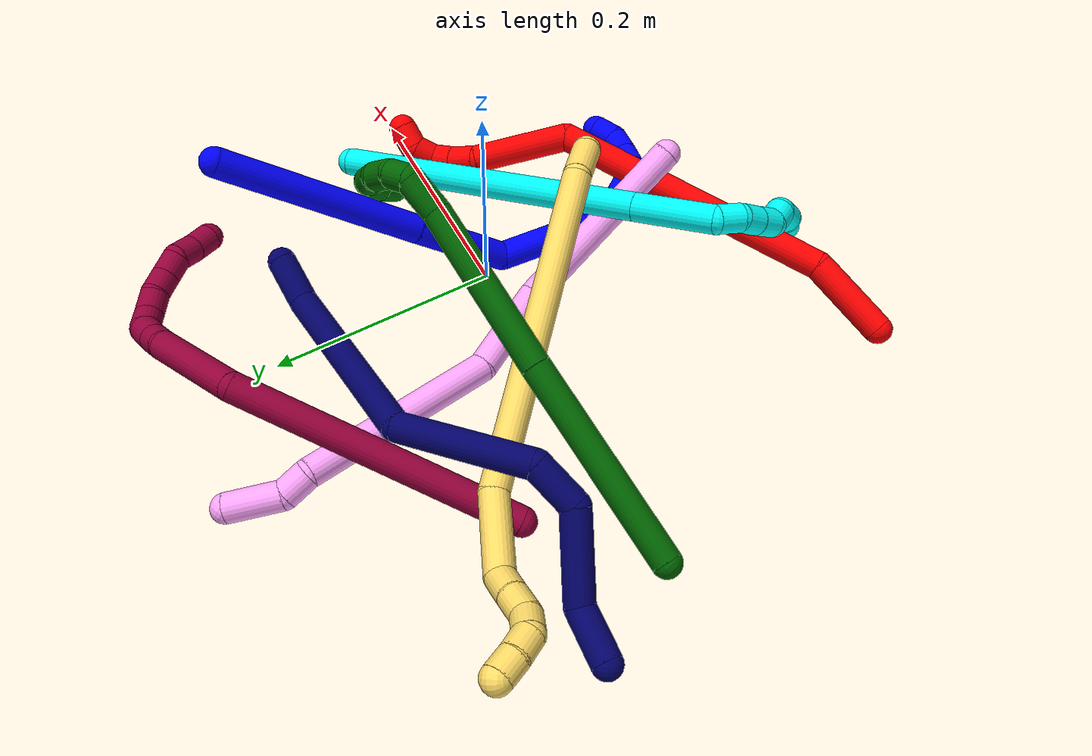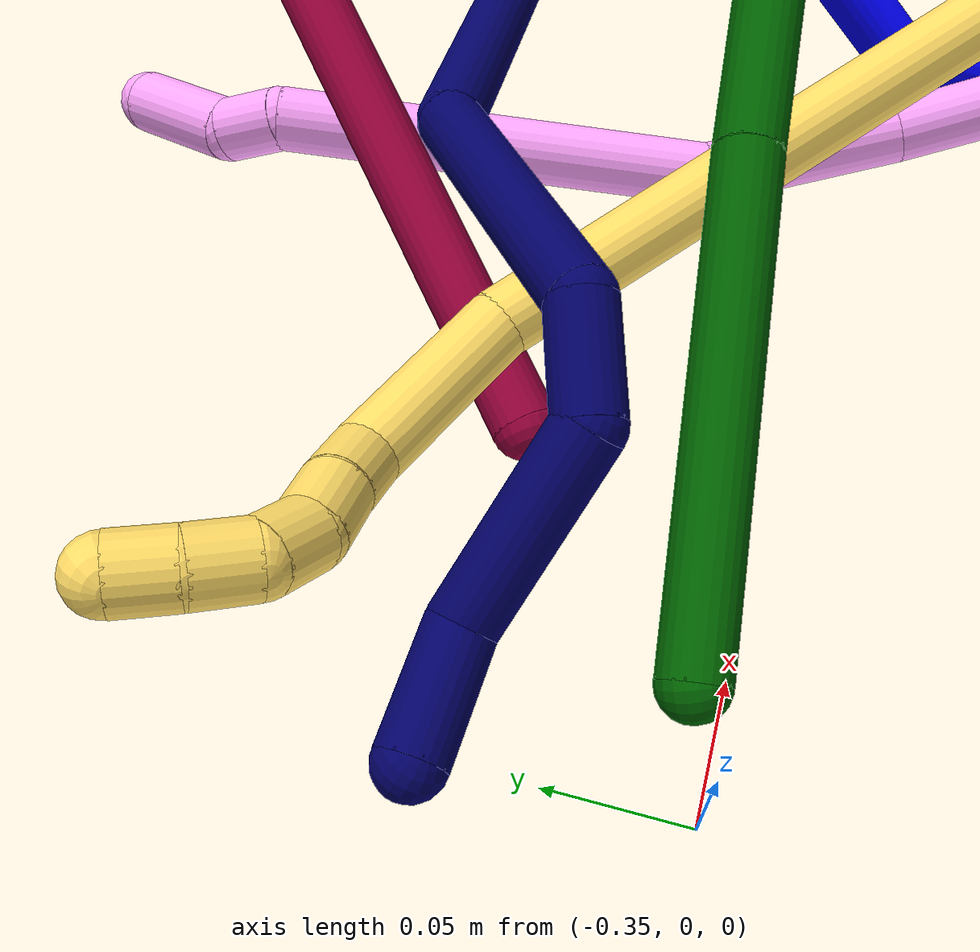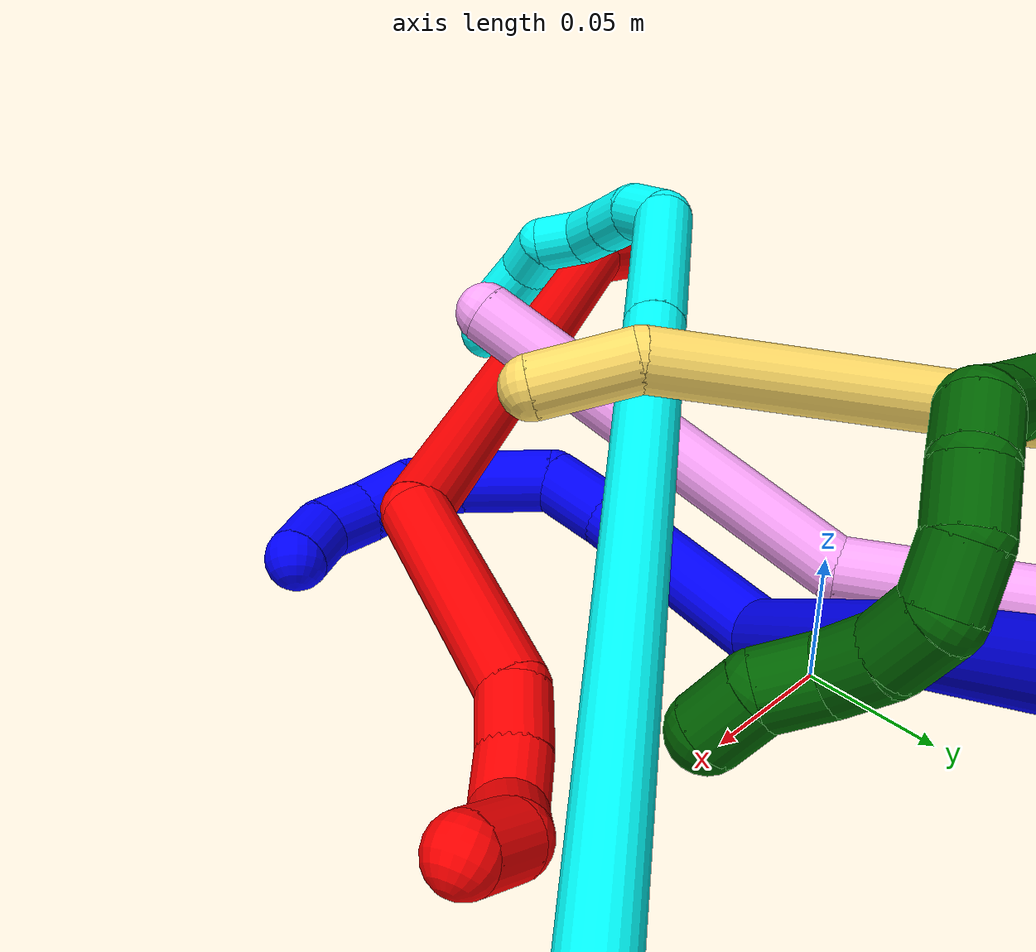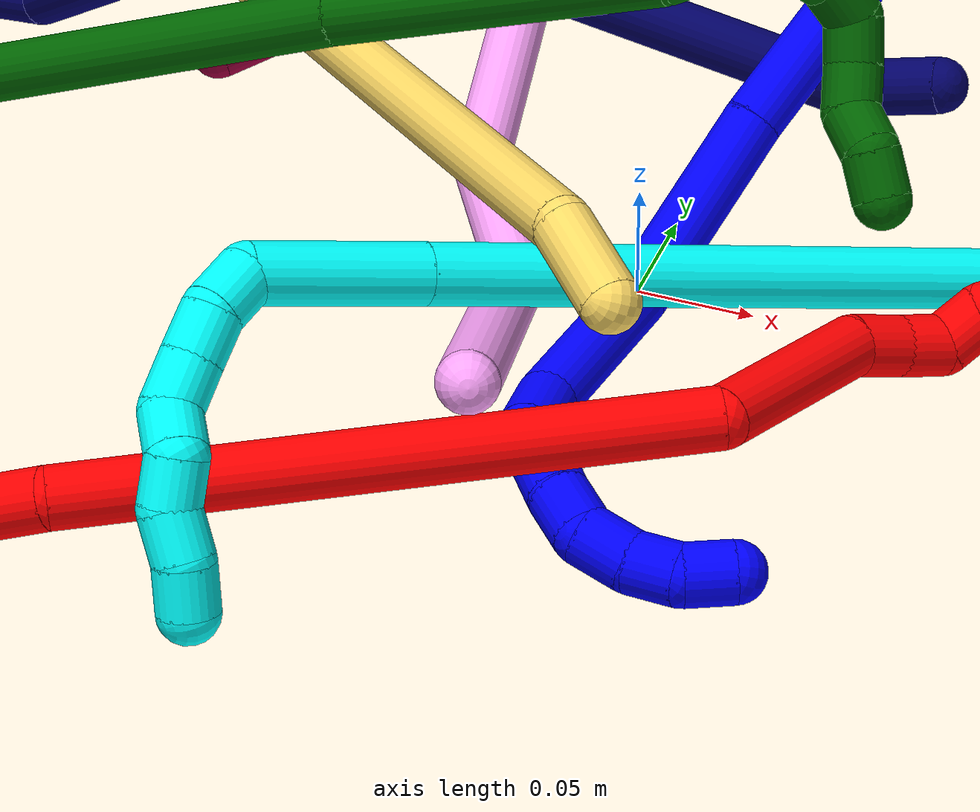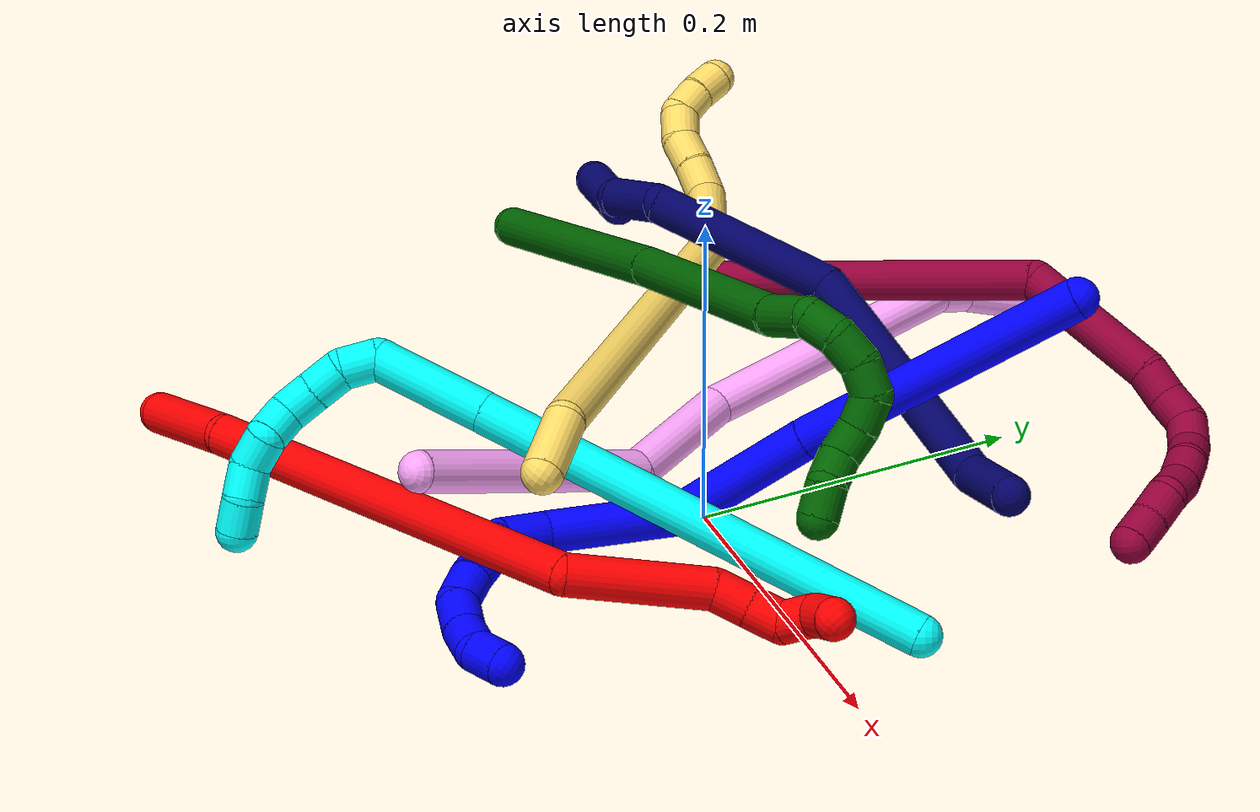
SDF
<sdf version="1.7">
 <world name="default">
  <plugin name="TubeGeneratorPlugin" filename="libtube_generator_plugin.so"/>
  <model name="photoneo_s_sensor">
   <static>1</static>
   <pose>0 0 2 1.57079 1.57079 3.14159</pose>
   <link name="link">
    <inertial><mass>0.1</mass></inertial>
    <sensor name="sensor" type="depth">
     <update_rate>30</update_rate>
     <camera>
      <horizontal_fov>1.22</horizontal_fov>
      <image><width>1920</width><height>1200</height><format>B8G8R8</format></image>
      <clip><near>0.1</near><far>4</far></clip>
      <depth_camera><output>points</output></depth_camera>
     </camera>
     <plugin name="camera_plugin" filename="libgazebo_ros_depth_camera.so">
      <baseline>0.2</baseline>
      <alwaysOn>1</alwaysOn>
      <updateRate>0.0</updateRate>
      <cameraName>camera_ir</cameraName>
      <imageTopicName>/camera/color/image_raw</imageTopicName>
      <cameraInfoTopicName>/camera/color/camera_info</cameraInfoTopicName>
      <depthImageTopicName>/camera/depth/image_raw</depthImageTopicName>
      <depthImageCameraInfoTopicName>/camera/depth/camera_info</depthImageCameraInfoTopicName>
      <pointCloudTopicName>/camera/depth/points</pointCloudTopicName>
      <frameName>fr_optical</frameName>
      <pointCloudCutoff>0.1</pointCloudCutoff>
      <pointCloudCutoffMax>2.0</pointCloudCutoffMax>
      <distortionK1>0</distortionK1>
      <distortionK2>0</distortionK2>
      <distortionK3>0</distortionK3>
      <distortionT1>0</distortionT1>
      <distortionT2>0</distortionT2>
      <CxPrime>0</CxPrime>
      <Cx>0</Cx>
      <Cy>0</Cy>
      <focalLength>0</focalLength>
      <hackBaseline>0</hackBaseline>
     </plugin>
    </sensor>
   </link>
  </model>
  <gravity>0 0 -9.8</gravity>
  <magnetic_field>6e-06 2.3e-05 -4.2e-05</magnetic_field>
  <atmosphere type="adiabatic"/>
  <physics name="default_physics" default="0" type="ode">
   <max_step_size>0.003</max_step_size>
   <real_time_factor>1</real_time_factor>
   <real_time_update_rate>1000</real_time_update_rate>
   <max_contacts>10000</max_contacts>
   <ode>
    <solver>
     <type>quick</type>
     <iters>100</iters>
     <sor>1.3</sor>
     <use_dynamic_moi_rescaling>0</use_dynamic_moi_rescaling>
    </solver>
    <constraints>
     <contact_max_correcting_vel>0</contact_max_correcting_vel>
     <contact_surface_layer>0.001</contact_surface_layer>
     <cfm>0</cfm>
     <erp>0.2</erp>
    </constraints>
   </ode>
  </physics>
  <scene><ambient>0.4 0.4 0.4 1</ambient><background>0.7 0.7 0.7 1</background><shadows>0</shadows></scene>
  <audio><device>default</device></audio>
  <spherical_coordinates>
   <surface_model>EARTH_WGS84</surface_model>
   <latitude_deg>0</latitude_deg>
   <longitude_deg>0</longitude_deg>
   <elevation>0</elevation>
   <heading_deg>0</heading_deg>
  </spherical_coordinates>
  <model name="bin">
   <static>1</static>
   <link name="bottom">
    <collision name="collision-bottom">
     <pose>0 0 -0.01 0 -0 0</pose>
     <geometry><box><size>0.8 0.6 0.02</size></box></geometry>
     <surface>
      <friction><ode><mu>100</mu><mu2>100</mu2></ode></friction>
      <contact><collide_bitmask>65535</collide_bitmask></contact>
     </surface>
    </collision>
   </link>
   <link name="west_wall">
    <collision name="collision-west_wall">
     <pose>-0.41 0 0.1 0 -0 0</pose>
     <geometry><box><size>0.02 0.6 0.2</size></box></geometry>
     <surface>
      <friction><ode><mu>100</mu><mu2>100</mu2></ode></friction>
      <contact><collide_bitmask>65535</collide_bitmask></contact>
     </surface>
    </collision>
   </link>
   <link name="east_wall">
    <collision name="collision-east_wall">
     <pose>0.41 0 0.1 0 -0 0</pose>
     <geometry><box><size>0.02 0.6 0.2</size></box></geometry>
     <surface>
      <friction><ode><mu>100</mu><mu2>100</mu2></ode></friction>
      <contact><collide_bitmask>65535</collide_bitmask></contact>
     </surface>
    </collision>
   </link>
   <link name="south_wall">
    <collision name="collision-south_wall">
     <pose>0 -0.31 0.1 0 -0 0</pose>
     <geometry><box><size>0.8 0.02 0.2</size></box></geometry>
     <surface>
      <friction><ode><mu>100</mu><mu2>100</mu2></ode></friction>
      <contact><collide_bitmask>65535</collide_bitmask></contact>
     </surface>
    </collision>
   </link>
   <link name="north_wall">
    <collision name="collision-north_wall">
     <pose>0 0.31 0.1 0 -0 0</pose>
     <geometry><box><size>0.8 0.02 0.2</size></box></geometry>
     <surface>
      <friction><ode><mu>100</mu><mu2>100</mu2></ode></friction>
      <contact><collide_bitmask>65535</collide_bitmask></contact>
     </surface>
    </collision>
   </link>
  </model>
  <model name="1">
   <static>0</static>
   <link name="1">
    <collision name="collision-cylinder-e_1_1_4">
     <pose>-0.057769 -0.057531 0.038666 0.979057 -0.694777 -0.38113</pose>
     <geometry><cylinder><radius>0.0125</radius><length>0.180468</length></cylinder></geometry>
     <surface>
      <friction><ode><mu>1.16</mu><mu2>1.16</mu2><slip1>0</slip1><slip2>0</slip2></ode></friction>
      <contact><ode><kp>1e+06</kp><kd>1</kd><max_vel>0</max_vel><min_depth>0.001</min_depth></ode></contact>
     </surface>
    </collision>
    <visual name="visual-cylinder-e_1_1_4">
     <pose>-0.057769 -0.057531 0.038666 0.979057 -0.694777 -0.38113</pose>
     <geometry><cylinder><radius>0.0125</radius><length>0.180468</length></cylinder></geometry>
     <material><ambient>0 0 1 1</ambient></material>
    </visual>
    <collision name="collision-cylinder-e_2_4_5">
     <pose>-0.14326 -0.145166 0.093952 1.06631 -0.678493 -0.410656</pose>
     <geometry><cylinder><radius>0.0125</radius><length>0.088339</length></cylinder></geometry>
     <surface>
      <friction><ode><mu>1.16</mu><mu2>1.16</mu2><slip1>0</slip1><slip2>0</slip2></ode></friction>
      <contact><ode><kp>1e+06</kp><kd>1</kd><max_vel>0</max_vel><min_depth>0.001</min_depth></ode></contact>
     </surface>
    </collision>
    <visual name="visual-cylinder-e_2_4_5">
     <pose>-0.14326 -0.145166 0.093952 1.06631 -0.678493 -0.410656</pose>
     <geometry><cylinder><radius>0.0125</radius><length>0.088339</length></cylinder></geometry>
     <material><ambient>0 0 1 1</ambient></material>
    </visual>
    <collision name="collision-cylinder-e_3_5_6">
     <pose>-0.172323 -0.202817 0.141374 0.729722 -0.032449 -0.012395</pose>
     <geometry><cylinder><radius>0.0125</radius><length>0.08269</length></cylinder></geometry>
     <surface>
      <friction><ode><mu>1.16</mu><mu2>1.16</mu2><slip1>0</slip1><slip2>0</slip2></ode></friction>
      <contact><ode><kp>1e+06</kp><kd>1</kd><max_vel>0</max_vel><min_depth>0.001</min_depth></ode></contact>
     </surface>
    </collision>
    <visual name="visual-cylinder-e_3_5_6">
     <pose>-0.172323 -0.202817 0.141374 0.729722 -0.032449 -0.012395</pose>
     <geometry><cylinder><radius>0.0125</radius><length>0.08269</length></cylinder></geometry>
     <material><ambient>0 0 1 1</ambient></material>
    </visual>
    <collision name="collision-cylinder-e_4_6_7">
     <pose>-0.170884 -0.240504 0.182005 0.800805 0.194392 0.082493</pose>
     <geometry><cylinder><radius>0.0125</radius><length>0.028787</length></cylinder></geometry>
     <surface>
      <friction><ode><mu>1.16</mu><mu2>1.16</mu2><slip1>0</slip1><slip2>0</slip2></ode></friction>
      <contact><ode><kp>1e+06</kp><kd>1</kd><max_vel>0</max_vel><min_depth>0.001</min_depth></ode></contact>
     </surface>
    </collision>
    <visual name="visual-cylinder-e_4_6_7">
     <pose>-0.170884 -0.240504 0.182005 0.800805 0.194392 0.082493</pose>
     <geometry><cylinder><radius>0.0125</radius><length>0.028787</length></cylinder></geometry>
     <material><ambient>0 0 1 1</ambient></material>
    </visual>
    <collision name="collision-cylinder-e_5_7_8">
     <pose>-0.161872 -0.267507 0.193747 1.45795 0.351904 0.314933</pose>
     <geometry><cylinder><radius>0.0125</radius><length>0.036159</length></cylinder></geometry>
     <surface>
      <friction><ode><mu>1.16</mu><mu2>1.16</mu2><slip1>0</slip1><slip2>0</slip2></ode></friction>
      <contact><ode><kp>1e+06</kp><kd>1</kd><max_vel>0</max_vel><min_depth>0.001</min_depth></ode></contact>
     </surface>
    </collision>
    <visual name="visual-cylinder-e_5_7_8">
     <pose>-0.161872 -0.267507 0.193747 1.45795 0.351904 0.314933</pose>
     <geometry><cylinder><radius>0.0125</radius><length>0.036159</length></cylinder></geometry>
     <material><ambient>0 0 1 1</ambient></material>
    </visual>
    <collision name="collision-cylinder-e_6_8_9">
     <pose>-0.151729 -0.294349 0.195339 1.60273 0.373334 0.385159</pose>
     <geometry><cylinder><radius>0.0125</radius><length>0.021444</length></cylinder></geometry>
     <surface>
      <friction><ode><mu>1.16</mu><mu2>1.16</mu2><slip1>0</slip1><slip2>0</slip2></ode></friction>
      <contact><ode><kp>1e+06</kp><kd>1</kd><max_vel>0</max_vel><min_depth>0.001</min_depth></ode></contact>
     </surface>
    </collision>
    <visual name="visual-cylinder-e_6_8_9">
     <pose>-0.151729 -0.294349 0.195339 1.60273 0.373334 0.385159</pose>
     <geometry><cylinder><radius>0.0125</radius><length>0.021444</length></cylinder></geometry>
     <material><ambient>0 0 1 1</ambient></material>
    </visual>
    <collision name="collision-cylinder-e_7_9_10">
     <pose>-0.142425 -0.312033 0.189659 2.17862 0.521503 0.944298</pose>
     <geometry><cylinder><radius>0.0125</radius><length>0.021654</length></cylinder></geometry>
     <surface>
      <friction><ode><mu>1.16</mu><mu2>1.16</mu2><slip1>0</slip1><slip2>0</slip2></ode></friction>
      <contact><ode><kp>1e+06</kp><kd>1</kd><max_vel>0</max_vel><min_depth>0.001</min_depth></ode></contact>
     </surface>
    </collision>
    <visual name="visual-cylinder-e_7_9_10">
     <pose>-0.142425 -0.312033 0.189659 2.17862 0.521503 0.944298</pose>
     <geometry><cylinder><radius>0.0125</radius><length>0.021654</length></cylinder></geometry>
     <material><ambient>0 0 1 1</ambient></material>
    </visual>
    <collision name="collision-cylinder-e_8_10_11">
     <pose>-0.13016 -0.325022 0.179177 2.34068 0.751231 1.49991</pose>
     <geometry><cylinder><radius>0.0125</radius><length>0.020134</length></cylinder></geometry>
     <surface>
      <friction><ode><mu>1.16</mu><mu2>1.16</mu2><slip1>0</slip1><slip2>0</slip2></ode></friction>
      <contact><ode><kp>1e+06</kp><kd>1</kd><max_vel>0</max_vel><min_depth>0.001</min_depth></ode></contact>
     </surface>
    </collision>
    <visual name="visual-cylinder-e_8_10_11">
     <pose>-0.13016 -0.325022 0.179177 2.34068 0.751231 1.49991</pose>
     <geometry><cylinder><radius>0.0125</radius><length>0.020134</length></cylinder></geometry>
     <material><ambient>0 0 1 1</ambient></material>
    </visual>
    <collision name="collision-cylinder-e_9_11_2">
     <pose>-0.117065 -0.331511 0.166112 2.99093 0.659067 2.7072</pose>
     <geometry><cylinder><radius>0.0125</radius><length>0.020326</length></cylinder></geometry>
     <surface>
      <friction><ode><mu>1.16</mu><mu2>1.16</mu2><slip1>0</slip1><slip2>0</slip2></ode></friction>
      <contact><ode><kp>1e+06</kp><kd>1</kd><max_vel>0</max_vel><min_depth>0.001</min_depth></ode></contact>
     </surface>
    </collision>
    <visual name="visual-cylinder-e_9_11_2">
     <pose>-0.117065 -0.331511 0.166112 2.99093 0.659067 2.7072</pose>
     <geometry><cylinder><radius>0.0125</radius><length>0.020326</length></cylinder></geometry>
     <material><ambient>0 0 1 1</ambient></material>
    </visual>
    <collision name="collision-sphere-2">
     <pose>-0.110841 -0.332717 0.158169 0 -0 0</pose>
     <geometry><sphere><radius>0.0125</radius></sphere></geometry>
     <surface>
      <friction><ode><mu>1.16</mu><mu2>1.16</mu2><slip1>0</slip1><slip2>0</slip2></ode></friction>
      <contact><ode><kp>1e+06</kp><kd>1</kd><max_vel>0</max_vel><min_depth>0.001</min_depth></ode></contact>
     </surface>
    </collision>
    <visual name="visual-sphere-2">
     <pose>-0.110841 -0.332717 0.158169 0 -0 0</pose>
     <geometry><sphere><radius>0.0125</radius></sphere></geometry>
     <material><ambient>0 0 1 1</ambient></material>
    </visual>
    <collision name="collision-sphere-11">
     <pose>-0.123289 -0.330305 0.174056 0 -0 0</pose>
     <geometry><sphere><radius>0.0125</radius></sphere></geometry>
     <surface>
      <friction><ode><mu>1.16</mu><mu2>1.16</mu2><slip1>0</slip1><slip2>0</slip2></ode></friction>
      <contact><ode><kp>1e+06</kp><kd>1</kd><max_vel>0</max_vel><min_depth>0.001</min_depth></ode></contact>
     </surface>
    </collision>
    <visual name="visual-sphere-11">
     <pose>-0.123289 -0.330305 0.174056 0 -0 0</pose>
     <geometry><sphere><radius>0.0125</radius></sphere></geometry>
     <material><ambient>0 0 1 1</ambient></material>
    </visual>
    <collision name="collision-sphere-10">
     <pose>-0.137031 -0.31974 0.184298 0 -0 0</pose>
     <geometry><sphere><radius>0.0125</radius></sphere></geometry>
     <surface>
      <friction><ode><mu>1.16</mu><mu2>1.16</mu2><slip1>0</slip1><slip2>0</slip2></ode></friction>
      <contact><ode><kp>1e+06</kp><kd>1</kd><max_vel>0</max_vel><min_depth>0.001</min_depth></ode></contact>
     </surface>
    </collision>
    <visual name="visual-sphere-10">
     <pose>-0.137031 -0.31974 0.184298 0 -0 0</pose>
     <geometry><sphere><radius>0.0125</radius></sphere></geometry>
     <material><ambient>0 0 1 1</ambient></material>
    </visual>
    <collision name="collision-sphere-9">
     <pose>-0.147819 -0.304327 0.19502 0 -0 0</pose>
     <geometry><sphere><radius>0.0125</radius></sphere></geometry>
     <surface>
      <friction><ode><mu>1.16</mu><mu2>1.16</mu2><slip1>0</slip1><slip2>0</slip2></ode></friction>
      <contact><ode><kp>1e+06</kp><kd>1</kd><max_vel>0</max_vel><min_depth>0.001</min_depth></ode></contact>
     </surface>
    </collision>
    <visual name="visual-sphere-9">
     <pose>-0.147819 -0.304327 0.19502 0 -0 0</pose>
     <geometry><sphere><radius>0.0125</radius></sphere></geometry>
     <material><ambient>0 0 1 1</ambient></material>
    </visual>
    <collision name="collision-sphere-4">
     <pose>-0.115538 -0.115063 0.077331 0 -0 0</pose>
     <geometry><sphere><radius>0.0125</radius></sphere></geometry>
     <surface>
      <friction><ode><mu>1.16</mu><mu2>1.16</mu2><slip1>0</slip1><slip2>0</slip2></ode></friction>
      <contact><ode><kp>1e+06</kp><kd>1</kd><max_vel>0</max_vel><min_depth>0.001</min_depth></ode></contact>
     </surface>
    </collision>
    <visual name="visual-sphere-4">
     <pose>-0.115538 -0.115063 0.077331 0 -0 0</pose>
     <geometry><sphere><radius>0.0125</radius></sphere></geometry>
     <material><ambient>0 0 1 1</ambient></material>
    </visual>
    <collision name="collision-sphere-1">
     <geometry><sphere><radius>0.0125</radius></sphere></geometry>
     <surface>
      <friction><ode><mu>1.16</mu><mu2>1.16</mu2><slip1>0</slip1><slip2>0</slip2></ode></friction>
      <contact><ode><kp>1e+06</kp><kd>1</kd><max_vel>0</max_vel><min_depth>0.001</min_depth></ode></contact>
     </surface>
    </collision>
    <visual name="visual-sphere-1">
     <geometry><sphere><radius>0.0125</radius></sphere></geometry>
     <material><ambient>0 0 1 1</ambient></material>
    </visual>
    <collision name="collision-sphere-8">
     <pose>-0.15564 -0.28437 0.195658 0 -0 0</pose>
     <geometry><sphere><radius>0.0125</radius></sphere></geometry>
     <surface>
      <friction><ode><mu>1.16</mu><mu2>1.16</mu2><slip1>0</slip1><slip2>0</slip2></ode></friction>
      <contact><ode><kp>1e+06</kp><kd>1</kd><max_vel>0</max_vel><min_depth>0.001</min_depth></ode></contact>
     </surface>
    </collision>
    <visual name="visual-sphere-8">
     <pose>-0.15564 -0.28437 0.195658 0 -0 0</pose>
     <geometry><sphere><radius>0.0125</radius></sphere></geometry>
     <material><ambient>0 0 1 1</ambient></material>
    </visual>
    <collision name="collision-sphere-5">
     <pose>-0.170981 -0.175269 0.110573 0 -0 0</pose>
     <geometry><sphere><radius>0.0125</radius></sphere></geometry>
     <surface>
      <friction><ode><mu>1.16</mu><mu2>1.16</mu2><slip1>0</slip1><slip2>0</slip2></ode></friction>
      <contact><ode><kp>1e+06</kp><kd>1</kd><max_vel>0</max_vel><min_depth>0.001</min_depth></ode></contact>
     </surface>
    </collision>
    <visual name="visual-sphere-5">
     <pose>-0.170981 -0.175269 0.110573 0 -0 0</pose>
     <geometry><sphere><radius>0.0125</radius></sphere></geometry>
     <material><ambient>0 0 1 1</ambient></material>
    </visual>
    <collision name="collision-sphere-6">
     <pose>-0.173664 -0.230366 0.172174 0 -0 0</pose>
     <geometry><sphere><radius>0.0125</radius></sphere></geometry>
     <surface>
      <friction><ode><mu>1.16</mu><mu2>1.16</mu2><slip1>0</slip1><slip2>0</slip2></ode></friction>
      <contact><ode><kp>1e+06</kp><kd>1</kd><max_vel>0</max_vel><min_depth>0.001</min_depth></ode></contact>
     </surface>
    </collision>
    <visual name="visual-sphere-6">
     <pose>-0.173664 -0.230366 0.172174 0 -0 0</pose>
     <geometry><sphere><radius>0.0125</radius></sphere></geometry>
     <material><ambient>0 0 1 1</ambient></material>
    </visual>
    <collision name="collision-sphere-7">
     <pose>-0.168103 -0.250643 0.191836 0 -0 0</pose>
     <geometry><sphere><radius>0.0125</radius></sphere></geometry>
     <surface>
      <friction><ode><mu>1.16</mu><mu2>1.16</mu2><slip1>0</slip1><slip2>0</slip2></ode></friction>
      <contact><ode><kp>1e+06</kp><kd>1</kd><max_vel>0</max_vel><min_depth>0.001</min_depth></ode></contact>
     </surface>
    </collision>
    <visual name="visual-sphere-7">
     <pose>-0.168103 -0.250643 0.191836 0 -0 0</pose>
     <geometry><sphere><radius>0.0125</radius></sphere></geometry>
     <material><ambient>0 0 1 1</ambient></material>
    </visual>
    <inertial>
     <pose>-0.118881 -0.165849 0.108985 0 -0 0</pose>
     <mass>0.5</mass>
     <inertia>
      <ixx>0.000292</ixx>
      <ixy>0</ixy>
      <ixz>0</ixz>
      <iyy>0.000257</iyy>
      <iyz>0</iyz>
      <izz>0.000767</izz>
     </inertia>
    </inertial>
   </link>
   <pose>0.096102 0.18786 0.157817 0.700076 -0.84079 0.014158</pose>
  </model>
  <model name="2">
   <static>0</static>
   <link name="2">
    <collision name="collision-cylinder-e_1_1_4">
     <pose>0.024475 0.000554 -0.027061 -3.12114 0.735164 -3.08849</pose>
     <geometry><cylinder><radius>0.0125</radius><length>0.072983</length></cylinder></geometry>
     <surface>
      <friction><ode><mu>1.16</mu><mu2>1.16</mu2><slip1>0</slip1><slip2>0</slip2></ode></friction>
      <contact><ode><kp>1e+06</kp><kd>1</kd><max_vel>0</max_vel><min_depth>0.001</min_depth></ode></contact>
     </surface>
    </collision>
    <visual name="visual-cylinder-e_1_1_4">
     <pose>0.024475 0.000554 -0.027061 -3.12114 0.735164 -3.08849</pose>
     <geometry><cylinder><radius>0.0125</radius><length>0.072983</length></cylinder></geometry>
     <material><ambient>1 0 0 1</ambient></material>
    </visual>
    <collision name="collision-cylinder-e_2_4_5">
     <pose>0.102149 0.028299 -0.166988 -2.90518 0.429673 -2.14474</pose>
     <geometry><cylinder><radius>0.0125</radius><length>0.255407</length></cylinder></geometry>
     <surface>
      <friction><ode><mu>1.16</mu><mu2>1.16</mu2><slip1>0</slip1><slip2>0</slip2></ode></friction>
      <contact><ode><kp>1e+06</kp><kd>1</kd><max_vel>0</max_vel><min_depth>0.001</min_depth></ode></contact>
     </surface>
    </collision>
    <visual name="visual-cylinder-e_2_4_5">
     <pose>0.102149 0.028299 -0.166988 -2.90518 0.429673 -2.14474</pose>
     <geometry><cylinder><radius>0.0125</radius><length>0.255407</length></cylinder></geometry>
     <material><ambient>1 0 0 1</ambient></material>
    </visual>
    <collision name="collision-cylinder-e_3_5_6">
     <pose>0.153456 0.08789 -0.308211 -2.28974 -0.043876 0.096646</pose>
     <geometry><cylinder><radius>0.0125</radius><length>0.086197</length></cylinder></geometry>
     <surface>
      <friction><ode><mu>1.16</mu><mu2>1.16</mu2><slip1>0</slip1><slip2>0</slip2></ode></friction>
      <contact><ode><kp>1e+06</kp><kd>1</kd><max_vel>0</max_vel><min_depth>0.001</min_depth></ode></contact>
     </surface>
    </collision>
    <visual name="visual-cylinder-e_3_5_6">
     <pose>0.153456 0.08789 -0.308211 -2.28974 -0.043876 0.096646</pose>
     <geometry><cylinder><radius>0.0125</radius><length>0.086197</length></cylinder></geometry>
     <material><ambient>1 0 0 1</ambient></material>
    </visual>
    <collision name="collision-cylinder-e_4_6_7">
     <pose>0.151392 0.12496 -0.346953 -2.71909 -0.015285 0.071247</pose>
     <geometry><cylinder><radius>0.0125</radius><length>0.022776</length></cylinder></geometry>
     <surface>
      <friction><ode><mu>1.16</mu><mu2>1.16</mu2><slip1>0</slip1><slip2>0</slip2></ode></friction>
      <contact><ode><kp>1e+06</kp><kd>1</kd><max_vel>0</max_vel><min_depth>0.001</min_depth></ode></contact>
     </surface>
    </collision>
    <visual name="visual-cylinder-e_4_6_7">
     <pose>0.151392 0.12496 -0.346953 -2.71909 -0.015285 0.071247</pose>
     <geometry><cylinder><radius>0.0125</radius><length>0.022776</length></cylinder></geometry>
     <material><ambient>1 0 0 1</ambient></material>
    </visual>
    <collision name="collision-cylinder-e_5_7_8">
     <pose>0.152266 0.133184 -0.366845 -2.78374 0.102985 -0.555204</pose>
     <geometry><cylinder><radius>0.0125</radius><length>0.020405</length></cylinder></geometry>
     <surface>
      <friction><ode><mu>1.16</mu><mu2>1.16</mu2><slip1>0</slip1><slip2>0</slip2></ode></friction>
      <contact><ode><kp>1e+06</kp><kd>1</kd><max_vel>0</max_vel><min_depth>0.001</min_depth></ode></contact>
     </surface>
    </collision>
    <visual name="visual-cylinder-e_5_7_8">
     <pose>0.152266 0.133184 -0.366845 -2.78374 0.102985 -0.555204</pose>
     <geometry><cylinder><radius>0.0125</radius><length>0.020405</length></cylinder></geometry>
     <material><ambient>1 0 0 1</ambient></material>
    </visual>
    <collision name="collision-cylinder-e_6_8_9">
     <pose>0.159946 0.142618 -0.381861 -2.32383 0.688511 -1.38251</pose>
     <geometry><cylinder><radius>0.0125</radius><length>0.020871</length></cylinder></geometry>
     <surface>
      <friction><ode><mu>1.16</mu><mu2>1.16</mu2><slip1>0</slip1><slip2>0</slip2></ode></friction>
      <contact><ode><kp>1e+06</kp><kd>1</kd><max_vel>0</max_vel><min_depth>0.001</min_depth></ode></contact>
     </surface>
    </collision>
    <visual name="visual-cylinder-e_6_8_9">
     <pose>0.159946 0.142618 -0.381861 -2.32383 0.688511 -1.38251</pose>
     <geometry><cylinder><radius>0.0125</radius><length>0.020871</length></cylinder></geometry>
     <material><ambient>1 0 0 1</ambient></material>
    </visual>
    <collision name="collision-cylinder-e_7_9_2">
     <pose>0.175145 0.147453 -0.39366 2.97709 0.931194 2.81634</pose>
     <geometry><cylinder><radius>0.0125</radius><length>0.021361</length></cylinder></geometry>
     <surface>
      <friction><ode><mu>1.16</mu><mu2>1.16</mu2><slip1>0</slip1><slip2>0</slip2></ode></friction>
      <contact><ode><kp>1e+06</kp><kd>1</kd><max_vel>0</max_vel><min_depth>0.001</min_depth></ode></contact>
     </surface>
    </collision>
    <visual name="visual-cylinder-e_7_9_2">
     <pose>0.175145 0.147453 -0.39366 2.97709 0.931194 2.81634</pose>
     <geometry><cylinder><radius>0.0125</radius><length>0.021361</length></cylinder></geometry>
     <material><ambient>1 0 0 1</ambient></material>
    </visual>
    <collision name="collision-sphere-2">
     <pose>0.183715 0.146409 -0.399949 0 -0 0</pose>
     <geometry><sphere><radius>0.0125</radius></sphere></geometry>
     <surface>
      <friction><ode><mu>1.16</mu><mu2>1.16</mu2><slip1>0</slip1><slip2>0</slip2></ode></friction>
      <contact><ode><kp>1e+06</kp><kd>1</kd><max_vel>0</max_vel><min_depth>0.001</min_depth></ode></contact>
     </surface>
    </collision>
    <visual name="visual-sphere-2">
     <pose>0.183715 0.146409 -0.399949 0 -0 0</pose>
     <geometry><sphere><radius>0.0125</radius></sphere></geometry>
     <material><ambient>1 0 0 1</ambient></material>
    </visual>
    <collision name="collision-sphere-9">
     <pose>0.166576 0.148497 -0.387371 0 -0 0</pose>
     <geometry><sphere><radius>0.0125</radius></sphere></geometry>
     <surface>
      <friction><ode><mu>1.16</mu><mu2>1.16</mu2><slip1>0</slip1><slip2>0</slip2></ode></friction>
      <contact><ode><kp>1e+06</kp><kd>1</kd><max_vel>0</max_vel><min_depth>0.001</min_depth></ode></contact>
     </surface>
    </collision>
    <visual name="visual-sphere-9">
     <pose>0.166576 0.148497 -0.387371 0 -0 0</pose>
     <geometry><sphere><radius>0.0125</radius></sphere></geometry>
     <material><ambient>1 0 0 1</ambient></material>
    </visual>
    <collision name="collision-sphere-4">
     <pose>0.048951 0.001107 -0.054122 0 -0 0</pose>
     <geometry><sphere><radius>0.0125</radius></sphere></geometry>
     <surface>
      <friction><ode><mu>1.16</mu><mu2>1.16</mu2><slip1>0</slip1><slip2>0</slip2></ode></friction>
      <contact><ode><kp>1e+06</kp><kd>1</kd><max_vel>0</max_vel><min_depth>0.001</min_depth></ode></contact>
     </surface>
    </collision>
    <visual name="visual-sphere-4">
     <pose>0.048951 0.001107 -0.054122 0 -0 0</pose>
     <geometry><sphere><radius>0.0125</radius></sphere></geometry>
     <material><ambient>1 0 0 1</ambient></material>
    </visual>
    <collision name="collision-sphere-1">
     <geometry><sphere><radius>0.0125</radius></sphere></geometry>
     <surface>
      <friction><ode><mu>1.16</mu><mu2>1.16</mu2><slip1>0</slip1><slip2>0</slip2></ode></friction>
      <contact><ode><kp>1e+06</kp><kd>1</kd><max_vel>0</max_vel><min_depth>0.001</min_depth></ode></contact>
     </surface>
    </collision>
    <visual name="visual-sphere-1">
     <geometry><sphere><radius>0.0125</radius></sphere></geometry>
     <material><ambient>1 0 0 1</ambient></material>
    </visual>
    <collision name="collision-sphere-8">
     <pose>0.153315 0.136738 -0.37635 0 -0 0</pose>
     <geometry><sphere><radius>0.0125</radius></sphere></geometry>
     <surface>
      <friction><ode><mu>1.16</mu><mu2>1.16</mu2><slip1>0</slip1><slip2>0</slip2></ode></friction>
      <contact><ode><kp>1e+06</kp><kd>1</kd><max_vel>0</max_vel><min_depth>0.001</min_depth></ode></contact>
     </surface>
    </collision>
    <visual name="visual-sphere-8">
     <pose>0.153315 0.136738 -0.37635 0 -0 0</pose>
     <geometry><sphere><radius>0.0125</radius></sphere></geometry>
     <material><ambient>1 0 0 1</ambient></material>
    </visual>
    <collision name="collision-sphere-5">
     <pose>0.155346 0.05549 -0.279854 0 -0 0</pose>
     <geometry><sphere><radius>0.0125</radius></sphere></geometry>
     <surface>
      <friction><ode><mu>1.16</mu><mu2>1.16</mu2><slip1>0</slip1><slip2>0</slip2></ode></friction>
      <contact><ode><kp>1e+06</kp><kd>1</kd><max_vel>0</max_vel><min_depth>0.001</min_depth></ode></contact>
     </surface>
    </collision>
    <visual name="visual-sphere-5">
     <pose>0.155346 0.05549 -0.279854 0 -0 0</pose>
     <geometry><sphere><radius>0.0125</radius></sphere></geometry>
     <material><ambient>1 0 0 1</ambient></material>
    </visual>
    <collision name="collision-sphere-6">
     <pose>0.151566 0.120291 -0.336568 0 -0 0</pose>
     <geometry><sphere><radius>0.0125</radius></sphere></geometry>
     <surface>
      <friction><ode><mu>1.16</mu><mu2>1.16</mu2><slip1>0</slip1><slip2>0</slip2></ode></friction>
      <contact><ode><kp>1e+06</kp><kd>1</kd><max_vel>0</max_vel><min_depth>0.001</min_depth></ode></contact>
     </surface>
    </collision>
    <visual name="visual-sphere-6">
     <pose>0.151566 0.120291 -0.336568 0 -0 0</pose>
     <geometry><sphere><radius>0.0125</radius></sphere></geometry>
     <material><ambient>1 0 0 1</ambient></material>
    </visual>
    <collision name="collision-sphere-7">
     <pose>0.151218 0.129629 -0.357339 0 -0 0</pose>
     <geometry><sphere><radius>0.0125</radius></sphere></geometry>
     <surface>
      <friction><ode><mu>1.16</mu><mu2>1.16</mu2><slip1>0</slip1><slip2>0</slip2></ode></friction>
      <contact><ode><kp>1e+06</kp><kd>1</kd><max_vel>0</max_vel><min_depth>0.001</min_depth></ode></contact>
     </surface>
    </collision>
    <visual name="visual-sphere-7">
     <pose>0.151218 0.129629 -0.357339 0 -0 0</pose>
     <geometry><sphere><radius>0.0125</radius></sphere></geometry>
     <material><ambient>1 0 0 1</ambient></material>
    </visual>
    <inertial>
     <pose>0.109475 0.053068 -0.205916 0 -0 0</pose>
     <mass>0.5</mass>
     <inertia>
      <ixx>-0.001708</ixx>
      <ixy>0</ixy>
      <ixz>0</ixz>
      <iyy>-0.000203</iyy>
      <iyz>0</iyz>
      <izz>-0.00098</izz>
     </inertia>
    </inertial>
   </link>
   <pose>-0.216011 -0.262583 0.016542 0.390888 -1.09659 -0.062134</pose>
  </model>
  <model name="3">
   <static>0</static>
   <link name="3">
    <collision name="collision-cylinder-e_1_1_4">
     <pose>-0.042125 -0.047841 0.127437 0.359126 -0.300119 -0.054876</pose>
     <geometry><cylinder><radius>0.0125</radius><length>0.284981</length></cylinder></geometry>
     <surface>
      <friction><ode><mu>1.16</mu><mu2>1.16</mu2><slip1>0</slip1><slip2>0</slip2></ode></friction>
      <contact><ode><kp>1e+06</kp><kd>1</kd><max_vel>0</max_vel><min_depth>0.001</min_depth></ode></contact>
     </surface>
    </collision>
    <visual name="visual-cylinder-e_1_1_4">
     <pose>-0.042125 -0.047841 0.127437 0.359126 -0.300119 -0.054876</pose>
     <geometry><cylinder><radius>0.0125</radius><length>0.284981</length></cylinder></geometry>
     <material><ambient>0.003922 1 0.996078 1</ambient></material>
    </visual>
    <collision name="collision-cylinder-e_2_4_5">
     <pose>-0.09476 -0.107532 0.286902 0.354392 -0.298581 -0.053856</pose>
     <geometry><cylinder><radius>0.0125</radius><length>0.071461</length></cylinder></geometry>
     <surface>
      <friction><ode><mu>1.16</mu><mu2>1.16</mu2><slip1>0</slip1><slip2>0</slip2></ode></friction>
      <contact><ode><kp>1e+06</kp><kd>1</kd><max_vel>0</max_vel><min_depth>0.001</min_depth></ode></contact>
     </surface>
    </collision>
    <visual name="visual-cylinder-e_2_4_5">
     <pose>-0.09476 -0.107532 0.286902 0.354392 -0.298581 -0.053856</pose>
     <geometry><cylinder><radius>0.0125</radius><length>0.071461</length></cylinder></geometry>
     <material><ambient>0.003922 1 0.996078 1</ambient></material>
    </visual>
    <collision name="collision-cylinder-e_3_5_6">
     <pose>-0.104336 -0.115747 0.329361 -0.3353 0.084405 -0.014293</pose>
     <geometry><cylinder><radius>0.0125</radius><length>0.022173</length></cylinder></geometry>
     <surface>
      <friction><ode><mu>1.16</mu><mu2>1.16</mu2><slip1>0</slip1><slip2>0</slip2></ode></friction>
      <contact><ode><kp>1e+06</kp><kd>1</kd><max_vel>0</max_vel><min_depth>0.001</min_depth></ode></contact>
     </surface>
    </collision>
    <visual name="visual-cylinder-e_3_5_6">
     <pose>-0.104336 -0.115747 0.329361 -0.3353 0.084405 -0.014293</pose>
     <geometry><cylinder><radius>0.0125</radius><length>0.022173</length></cylinder></geometry>
     <material><ambient>0.003922 1 0.996078 1</ambient></material>
    </visual>
    <collision name="collision-cylinder-e_4_6_7">
     <pose>-0.098685 -0.10818 0.347731 -0.459896 0.489286 -0.116744</pose>
     <geometry><cylinder><radius>0.0125</radius><length>0.020073</length></cylinder></geometry>
     <surface>
      <friction><ode><mu>1.16</mu><mu2>1.16</mu2><slip1>0</slip1><slip2>0</slip2></ode></friction>
      <contact><ode><kp>1e+06</kp><kd>1</kd><max_vel>0</max_vel><min_depth>0.001</min_depth></ode></contact>
     </surface>
    </collision>
    <visual name="visual-cylinder-e_4_6_7">
     <pose>-0.098685 -0.10818 0.347731 -0.459896 0.489286 -0.116744</pose>
     <geometry><cylinder><radius>0.0125</radius><length>0.020073</length></cylinder></geometry>
     <material><ambient>0.003922 1 0.996078 1</ambient></material>
    </visual>
    <collision name="collision-cylinder-e_5_7_8">
     <pose>-0.089188 -0.09972 0.363981 -0.498835 0.467659 -0.121194</pose>
     <geometry><cylinder><radius>0.0125</radius><length>0.021206</length></cylinder></geometry>
     <surface>
      <friction><ode><mu>1.16</mu><mu2>1.16</mu2><slip1>0</slip1><slip2>0</slip2></ode></friction>
      <contact><ode><kp>1e+06</kp><kd>1</kd><max_vel>0</max_vel><min_depth>0.001</min_depth></ode></contact>
     </surface>
    </collision>
    <visual name="visual-cylinder-e_5_7_8">
     <pose>-0.089188 -0.09972 0.363981 -0.498835 0.467659 -0.121194</pose>
     <geometry><cylinder><radius>0.0125</radius><length>0.021206</length></cylinder></geometry>
     <material><ambient>0.003922 1 0.996078 1</ambient></material>
    </visual>
    <collision name="collision-cylinder-e_6_8_9">
     <pose>-0.082584 -0.086379 0.376704 -1.10667 0.182931 -0.113192</pose>
     <geometry><cylinder><radius>0.0125</radius><length>0.020047</length></cylinder></geometry>
     <surface>
      <friction><ode><mu>1.16</mu><mu2>1.16</mu2><slip1>0</slip1><slip2>0</slip2></ode></friction>
      <contact><ode><kp>1e+06</kp><kd>1</kd><max_vel>0</max_vel><min_depth>0.001</min_depth></ode></contact>
     </surface>
    </collision>
    <visual name="visual-cylinder-e_6_8_9">
     <pose>-0.082584 -0.086379 0.376704 -1.10667 0.182931 -0.113192</pose>
     <geometry><cylinder><radius>0.0125</radius><length>0.020047</length></cylinder></geometry>
     <material><ambient>0.003922 1 0.996078 1</ambient></material>
    </visual>
    <collision name="collision-cylinder-e_7_9_10">
     <pose>-0.07327 -0.073566 0.386408 -0.647182 0.8461 -0.299735</pose>
     <geometry><cylinder><radius>0.0125</radius><length>0.020011</length></cylinder></geometry>
     <surface>
      <friction><ode><mu>1.16</mu><mu2>1.16</mu2><slip1>0</slip1><slip2>0</slip2></ode></friction>
      <contact><ode><kp>1e+06</kp><kd>1</kd><max_vel>0</max_vel><min_depth>0.001</min_depth></ode></contact>
     </surface>
    </collision>
    <visual name="visual-cylinder-e_7_9_10">
     <pose>-0.07327 -0.073566 0.386408 -0.647182 0.8461 -0.299735</pose>
     <geometry><cylinder><radius>0.0125</radius><length>0.020011</length></cylinder></geometry>
     <material><ambient>0.003922 1 0.996078 1</ambient></material>
    </visual>
    <collision name="collision-cylinder-e_8_10_11">
     <pose>-0.058469 -0.062979 0.393566 -1.29477 0.818037 -0.633411</pose>
     <geometry><cylinder><radius>0.0125</radius><length>0.020031</length></cylinder></geometry>
     <surface>
      <friction><ode><mu>1.16</mu><mu2>1.16</mu2><slip1>0</slip1><slip2>0</slip2></ode></friction>
      <contact><ode><kp>1e+06</kp><kd>1</kd><max_vel>0</max_vel><min_depth>0.001</min_depth></ode></contact>
     </surface>
    </collision>
    <visual name="visual-cylinder-e_8_10_11">
     <pose>-0.058469 -0.062979 0.393566 -1.29477 0.818037 -0.633411</pose>
     <geometry><cylinder><radius>0.0125</radius><length>0.020031</length></cylinder></geometry>
     <material><ambient>0.003922 1 0.996078 1</ambient></material>
    </visual>
    <collision name="collision-cylinder-e_9_11_2">
     <pose>-0.042281 -0.05253 0.397969 -0.98932 1.09101 -0.632754</pose>
     <geometry><cylinder><radius>0.0125</radius><length>0.020017</length></cylinder></geometry>
     <surface>
      <friction><ode><mu>1.16</mu><mu2>1.16</mu2><slip1>0</slip1><slip2>0</slip2></ode></friction>
      <contact><ode><kp>1e+06</kp><kd>1</kd><max_vel>0</max_vel><min_depth>0.001</min_depth></ode></contact>
     </surface>
    </collision>
    <visual name="visual-cylinder-e_9_11_2">
     <pose>-0.042281 -0.05253 0.397969 -0.98932 1.09101 -0.632754</pose>
     <geometry><cylinder><radius>0.0125</radius><length>0.020017</length></cylinder></geometry>
     <material><ambient>0.003922 1 0.996078 1</ambient></material>
    </visual>
    <collision name="collision-sphere-2">
     <pose>-0.033403 -0.04867 0.400507 0 -0 0</pose>
     <geometry><sphere><radius>0.0125</radius></sphere></geometry>
     <surface>
      <friction><ode><mu>1.16</mu><mu2>1.16</mu2><slip1>0</slip1><slip2>0</slip2></ode></friction>
      <contact><ode><kp>1e+06</kp><kd>1</kd><max_vel>0</max_vel><min_depth>0.001</min_depth></ode></contact>
     </surface>
    </collision>
    <visual name="visual-sphere-2">
     <pose>-0.033403 -0.04867 0.400507 0 -0 0</pose>
     <geometry><sphere><radius>0.0125</radius></sphere></geometry>
     <material><ambient>0.003922 1 0.996078 1</ambient></material>
    </visual>
    <collision name="collision-sphere-11">
     <pose>-0.05116 -0.056391 0.395432 0 -0 0</pose>
     <geometry><sphere><radius>0.0125</radius></sphere></geometry>
     <surface>
      <friction><ode><mu>1.16</mu><mu2>1.16</mu2><slip1>0</slip1><slip2>0</slip2></ode></friction>
      <contact><ode><kp>1e+06</kp><kd>1</kd><max_vel>0</max_vel><min_depth>0.001</min_depth></ode></contact>
     </surface>
    </collision>
    <visual name="visual-sphere-11">
     <pose>-0.05116 -0.056391 0.395432 0 -0 0</pose>
     <geometry><sphere><radius>0.0125</radius></sphere></geometry>
     <material><ambient>0.003922 1 0.996078 1</ambient></material>
    </visual>
    <collision name="collision-sphere-10">
     <pose>-0.065779 -0.069567 0.3917 0 -0 0</pose>
     <geometry><sphere><radius>0.0125</radius></sphere></geometry>
     <surface>
      <friction><ode><mu>1.16</mu><mu2>1.16</mu2><slip1>0</slip1><slip2>0</slip2></ode></friction>
      <contact><ode><kp>1e+06</kp><kd>1</kd><max_vel>0</max_vel><min_depth>0.001</min_depth></ode></contact>
     </surface>
    </collision>
    <visual name="visual-sphere-10">
     <pose>-0.065779 -0.069567 0.3917 0 -0 0</pose>
     <geometry><sphere><radius>0.0125</radius></sphere></geometry>
     <material><ambient>0.003922 1 0.996078 1</ambient></material>
    </visual>
    <collision name="collision-sphere-9">
     <pose>-0.080761 -0.077565 0.381116 0 -0 0</pose>
     <geometry><sphere><radius>0.0125</radius></sphere></geometry>
     <surface>
      <friction><ode><mu>1.16</mu><mu2>1.16</mu2><slip1>0</slip1><slip2>0</slip2></ode></friction>
      <contact><ode><kp>1e+06</kp><kd>1</kd><max_vel>0</max_vel><min_depth>0.001</min_depth></ode></contact>
     </surface>
    </collision>
    <visual name="visual-sphere-9">
     <pose>-0.080761 -0.077565 0.381116 0 -0 0</pose>
     <geometry><sphere><radius>0.0125</radius></sphere></geometry>
     <material><ambient>0.003922 1 0.996078 1</ambient></material>
    </visual>
    <collision name="collision-sphere-4">
     <pose>-0.08425 -0.095681 0.254875 0 -0 0</pose>
     <geometry><sphere><radius>0.0125</radius></sphere></geometry>
     <surface>
      <friction><ode><mu>1.16</mu><mu2>1.16</mu2><slip1>0</slip1><slip2>0</slip2></ode></friction>
      <contact><ode><kp>1e+06</kp><kd>1</kd><max_vel>0</max_vel><min_depth>0.001</min_depth></ode></contact>
     </surface>
    </collision>
    <visual name="visual-sphere-4">
     <pose>-0.08425 -0.095681 0.254875 0 -0 0</pose>
     <geometry><sphere><radius>0.0125</radius></sphere></geometry>
     <material><ambient>0.003922 1 0.996078 1</ambient></material>
    </visual>
    <collision name="collision-sphere-1">
     <geometry><sphere><radius>0.0125</radius></sphere></geometry>
     <surface>
      <friction><ode><mu>1.16</mu><mu2>1.16</mu2><slip1>0</slip1><slip2>0</slip2></ode></friction>
      <contact><ode><kp>1e+06</kp><kd>1</kd><max_vel>0</max_vel><min_depth>0.001</min_depth></ode></contact>
     </surface>
    </collision>
    <visual name="visual-sphere-1">
     <geometry><sphere><radius>0.0125</radius></sphere></geometry>
     <material><ambient>0.003922 1 0.996078 1</ambient></material>
    </visual>
    <collision name="collision-sphere-8">
     <pose>-0.084408 -0.095192 0.372292 0 -0 0</pose>
     <geometry><sphere><radius>0.0125</radius></sphere></geometry>
     <surface>
      <friction><ode><mu>1.16</mu><mu2>1.16</mu2><slip1>0</slip1><slip2>0</slip2></ode></friction>
      <contact><ode><kp>1e+06</kp><kd>1</kd><max_vel>0</max_vel><min_depth>0.001</min_depth></ode></contact>
     </surface>
    </collision>
    <visual name="visual-sphere-8">
     <pose>-0.084408 -0.095192 0.372292 0 -0 0</pose>
     <geometry><sphere><radius>0.0125</radius></sphere></geometry>
     <material><ambient>0.003922 1 0.996078 1</ambient></material>
    </visual>
    <collision name="collision-sphere-5">
     <pose>-0.105271 -0.119382 0.318929 0 -0 0</pose>
     <geometry><sphere><radius>0.0125</radius></sphere></geometry>
     <surface>
      <friction><ode><mu>1.16</mu><mu2>1.16</mu2><slip1>0</slip1><slip2>0</slip2></ode></friction>
      <contact><ode><kp>1e+06</kp><kd>1</kd><max_vel>0</max_vel><min_depth>0.001</min_depth></ode></contact>
     </surface>
    </collision>
    <visual name="visual-sphere-5">
     <pose>-0.105271 -0.119382 0.318929 0 -0 0</pose>
     <geometry><sphere><radius>0.0125</radius></sphere></geometry>
     <material><ambient>0.003922 1 0.996078 1</ambient></material>
    </visual>
    <collision name="collision-sphere-6">
     <pose>-0.103402 -0.112112 0.339793 0 -0 0</pose>
     <geometry><sphere><radius>0.0125</radius></sphere></geometry>
     <surface>
      <friction><ode><mu>1.16</mu><mu2>1.16</mu2><slip1>0</slip1><slip2>0</slip2></ode></friction>
      <contact><ode><kp>1e+06</kp><kd>1</kd><max_vel>0</max_vel><min_depth>0.001</min_depth></ode></contact>
     </surface>
    </collision>
    <visual name="visual-sphere-6">
     <pose>-0.103402 -0.112112 0.339793 0 -0 0</pose>
     <geometry><sphere><radius>0.0125</radius></sphere></geometry>
     <material><ambient>0.003922 1 0.996078 1</ambient></material>
    </visual>
    <collision name="collision-sphere-7">
     <pose>-0.093967 -0.104248 0.35567 0 -0 0</pose>
     <geometry><sphere><radius>0.0125</radius></sphere></geometry>
     <surface>
      <friction><ode><mu>1.16</mu><mu2>1.16</mu2><slip1>0</slip1><slip2>0</slip2></ode></friction>
      <contact><ode><kp>1e+06</kp><kd>1</kd><max_vel>0</max_vel><min_depth>0.001</min_depth></ode></contact>
     </surface>
    </collision>
    <visual name="visual-sphere-7">
     <pose>-0.093967 -0.104248 0.35567 0 -0 0</pose>
     <geometry><sphere><radius>0.0125</radius></sphere></geometry>
     <material><ambient>0.003922 1 0.996078 1</ambient></material>
    </visual>
    <inertial>
     <pose>-0.060203 -0.067375 0.21991 0 -0 0</pose>
     <mass>0.5</mass>
     <inertia>
      <ixx>0.001782</ixx>
      <ixy>0</ixy>
      <ixz>0</ixz>
      <iyy>0.001755</iyy>
      <iyz>0</iyz>
      <izz>0.001266</izz>
     </inertia>
    </inertial>
   </link>
   <pose>0.169874 0.05431 0.012186 -2.46184 1.45348 1.68573</pose>
  </model>
  <model name="4">
   <static>0</static>
   <link name="4">
    <collision name="collision-cylinder-e_1_1_4">
     <pose>-0.012169 -0.003093 0.083618 0.036973 -0.144413 -0.002675</pose>
     <geometry><cylinder><radius>0.0125</radius><length>0.169111</length></cylinder></geometry>
     <surface>
      <friction><ode><mu>1.16</mu><mu2>1.16</mu2><slip1>0</slip1><slip2>0</slip2></ode></friction>
      <contact><ode><kp>1e+06</kp><kd>1</kd><max_vel>0</max_vel><min_depth>0.001</min_depth></ode></contact>
     </surface>
    </collision>
    <visual name="visual-cylinder-e_1_1_4">
     <pose>-0.012169 -0.003093 0.083618 0.036973 -0.144413 -0.002675</pose>
     <geometry><cylinder><radius>0.0125</radius><length>0.169111</length></cylinder></geometry>
     <material><ambient>1 0.65098 0.996078 1</ambient></material>
    </visual>
    <collision name="collision-cylinder-e_2_4_5">
     <pose>-0.0265 0.012284 0.205393 -0.450808 -0.050969 0.01169</pose>
     <geometry><cylinder><radius>0.0125</radius><length>0.084893</length></cylinder></geometry>
     <surface>
      <friction><ode><mu>1.16</mu><mu2>1.16</mu2><slip1>0</slip1><slip2>0</slip2></ode></friction>
      <contact><ode><kp>1e+06</kp><kd>1</kd><max_vel>0</max_vel><min_depth>0.001</min_depth></ode></contact>
     </surface>
    </collision>
    <visual name="visual-cylinder-e_2_4_5">
     <pose>-0.0265 0.012284 0.205393 -0.450808 -0.050969 0.01169</pose>
     <geometry><cylinder><radius>0.0125</radius><length>0.084893</length></cylinder></geometry>
     <material><ambient>1 0.65098 0.996078 1</ambient></material>
    </visual>
    <collision name="collision-cylinder-e_3_5_6">
     <pose>-0.064228 0.062378 0.316178 -0.410676 -0.422006 0.089162</pose>
     <geometry><cylinder><radius>0.0125</radius><length>0.173666</length></cylinder></geometry>
     <surface>
      <friction><ode><mu>1.16</mu><mu2>1.16</mu2><slip1>0</slip1><slip2>0</slip2></ode></friction>
      <contact><ode><kp>1e+06</kp><kd>1</kd><max_vel>0</max_vel><min_depth>0.001</min_depth></ode></contact>
     </surface>
    </collision>
    <visual name="visual-cylinder-e_3_5_6">
     <pose>-0.064228 0.062378 0.316178 -0.410676 -0.422006 0.089162</pose>
     <geometry><cylinder><radius>0.0125</radius><length>0.173666</length></cylinder></geometry>
     <material><ambient>1 0.65098 0.996078 1</ambient></material>
    </visual>
    <collision name="collision-cylinder-e_4_6_7">
     <pose>-0.102515 0.094189 0.400639 -0.015688 -0.225994 0.00178</pose>
     <geometry><cylinder><radius>0.0125</radius><length>0.024286</length></cylinder></geometry>
     <surface>
      <friction><ode><mu>1.16</mu><mu2>1.16</mu2><slip1>0</slip1><slip2>0</slip2></ode></friction>
      <contact><ode><kp>1e+06</kp><kd>1</kd><max_vel>0</max_vel><min_depth>0.001</min_depth></ode></contact>
     </surface>
    </collision>
    <visual name="visual-cylinder-e_4_6_7">
     <pose>-0.102515 0.094189 0.400639 -0.015688 -0.225994 0.00178</pose>
     <geometry><cylinder><radius>0.0125</radius><length>0.024286</length></cylinder></geometry>
     <material><ambient>1 0.65098 0.996078 1</ambient></material>
    </visual>
    <collision name="collision-cylinder-e_5_7_2">
     <pose>-0.120883 0.090076 0.430184 0.238099 -0.709397 -0.088544</pose>
     <geometry><cylinder><radius>0.0125</radius><length>0.048043</length></cylinder></geometry>
     <surface>
      <friction><ode><mu>1.16</mu><mu2>1.16</mu2><slip1>0</slip1><slip2>0</slip2></ode></friction>
      <contact><ode><kp>1e+06</kp><kd>1</kd><max_vel>0</max_vel><min_depth>0.001</min_depth></ode></contact>
     </surface>
    </collision>
    <visual name="visual-cylinder-e_5_7_2">
     <pose>-0.120883 0.090076 0.430184 0.238099 -0.709397 -0.088544</pose>
     <geometry><cylinder><radius>0.0125</radius><length>0.048043</length></cylinder></geometry>
     <material><ambient>1 0.65098 0.996078 1</ambient></material>
    </visual>
    <collision name="collision-sphere-2">
     <pose>-0.13653 0.085777 0.447897 0 -0 0</pose>
     <geometry><sphere><radius>0.0125</radius></sphere></geometry>
     <surface>
      <friction><ode><mu>1.16</mu><mu2>1.16</mu2><slip1>0</slip1><slip2>0</slip2></ode></friction>
      <contact><ode><kp>1e+06</kp><kd>1</kd><max_vel>0</max_vel><min_depth>0.001</min_depth></ode></contact>
     </surface>
    </collision>
    <visual name="visual-sphere-2">
     <pose>-0.13653 0.085777 0.447897 0 -0 0</pose>
     <geometry><sphere><radius>0.0125</radius></sphere></geometry>
     <material><ambient>1 0.65098 0.996078 1</ambient></material>
    </visual>
    <collision name="collision-sphere-7">
     <pose>-0.105236 0.094375 0.412472 0 -0 0</pose>
     <geometry><sphere><radius>0.0125</radius></sphere></geometry>
     <surface>
      <friction><ode><mu>1.16</mu><mu2>1.16</mu2><slip1>0</slip1><slip2>0</slip2></ode></friction>
      <contact><ode><kp>1e+06</kp><kd>1</kd><max_vel>0</max_vel><min_depth>0.001</min_depth></ode></contact>
     </surface>
    </collision>
    <visual name="visual-sphere-7">
     <pose>-0.105236 0.094375 0.412472 0 -0 0</pose>
     <geometry><sphere><radius>0.0125</radius></sphere></geometry>
     <material><ambient>1 0.65098 0.996078 1</ambient></material>
    </visual>
    <collision name="collision-sphere-6">
     <pose>-0.099794 0.094003 0.388806 0 -0 0</pose>
     <geometry><sphere><radius>0.0125</radius></sphere></geometry>
     <surface>
      <friction><ode><mu>1.16</mu><mu2>1.16</mu2><slip1>0</slip1><slip2>0</slip2></ode></friction>
      <contact><ode><kp>1e+06</kp><kd>1</kd><max_vel>0</max_vel><min_depth>0.001</min_depth></ode></contact>
     </surface>
    </collision>
    <visual name="visual-sphere-6">
     <pose>-0.099794 0.094003 0.388806 0 -0 0</pose>
     <geometry><sphere><radius>0.0125</radius></sphere></geometry>
     <material><ambient>1 0.65098 0.996078 1</ambient></material>
    </visual>
    <collision name="collision-sphere-5">
     <pose>-0.028662 0.030753 0.243549 0 -0 0</pose>
     <geometry><sphere><radius>0.0125</radius></sphere></geometry>
     <surface>
      <friction><ode><mu>1.16</mu><mu2>1.16</mu2><slip1>0</slip1><slip2>0</slip2></ode></friction>
      <contact><ode><kp>1e+06</kp><kd>1</kd><max_vel>0</max_vel><min_depth>0.001</min_depth></ode></contact>
     </surface>
    </collision>
    <visual name="visual-sphere-5">
     <pose>-0.028662 0.030753 0.243549 0 -0 0</pose>
     <geometry><sphere><radius>0.0125</radius></sphere></geometry>
     <material><ambient>1 0.65098 0.996078 1</ambient></material>
    </visual>
    <collision name="collision-sphere-1">
     <geometry><sphere><radius>0.0125</radius></sphere></geometry>
     <surface>
      <friction><ode><mu>1.16</mu><mu2>1.16</mu2><slip1>0</slip1><slip2>0</slip2></ode></friction>
      <contact><ode><kp>1e+06</kp><kd>1</kd><max_vel>0</max_vel><min_depth>0.001</min_depth></ode></contact>
     </surface>
    </collision>
    <visual name="visual-sphere-1">
     <geometry><sphere><radius>0.0125</radius></sphere></geometry>
     <material><ambient>1 0.65098 0.996078 1</ambient></material>
    </visual>
    <collision name="collision-sphere-4">
     <pose>-0.024337 -0.006186 0.167236 0 -0 0</pose>
     <geometry><sphere><radius>0.0125</radius></sphere></geometry>
     <surface>
      <friction><ode><mu>1.16</mu><mu2>1.16</mu2><slip1>0</slip1><slip2>0</slip2></ode></friction>
      <contact><ode><kp>1e+06</kp><kd>1</kd><max_vel>0</max_vel><min_depth>0.001</min_depth></ode></contact>
     </surface>
    </collision>
    <visual name="visual-sphere-4">
     <pose>-0.024337 -0.006186 0.167236 0 -0 0</pose>
     <geometry><sphere><radius>0.0125</radius></sphere></geometry>
     <material><ambient>1 0.65098 0.996078 1</ambient></material>
    </visual>
    <inertial>
     <pose>-0.047518 0.035936 0.233768 0 -0 0</pose>
     <mass>0.5</mass>
     <inertia>
      <ixx>0.000897</ixx>
      <ixy>0</ixy>
      <ixz>0</ixz>
      <iyy>0.000924</iyy>
      <iyz>0</iyz>
      <izz>0.000118</izz>
     </inertia>
    </inertial>
   </link>
   <pose>-0.007467 -0.174011 0.07876 2.05468 0.414107 -2.53441</pose>
  </model>
  <model name="5">
   <static>0</static>
   <link name="5">
    <collision name="collision-cylinder-e_1_1_4">
     <pose>-0.016897 0.010982 -0.00319 -1.85348 -0.9758 1.23052</pose>
     <geometry><cylinder><radius>0.0125</radius><length>0.040806</length></cylinder></geometry>
     <surface>
      <friction><ode><mu>1.16</mu><mu2>1.16</mu2><slip1>0</slip1><slip2>0</slip2></ode></friction>
      <contact><ode><kp>1e+06</kp><kd>1</kd><max_vel>0</max_vel><min_depth>0.001</min_depth></ode></contact>
     </surface>
    </collision>
    <visual name="visual-cylinder-e_1_1_4">
     <pose>-0.016897 0.010982 -0.00319 -1.85348 -0.9758 1.23052</pose>
     <geometry><cylinder><radius>0.0125</radius><length>0.040806</length></cylinder></geometry>
     <material><ambient>1 0.858824 0.4 1</ambient></material>
    </visual>
    <collision name="collision-cylinder-e_2_4_5">
     <pose>-0.115514 0.138221 0.001767 -1.50083 -0.611539 0.572478</pose>
     <geometry><cylinder><radius>0.0125</radius><length>0.284677</length></cylinder></geometry>
     <surface>
      <friction><ode><mu>1.16</mu><mu2>1.16</mu2><slip1>0</slip1><slip2>0</slip2></ode></friction>
      <contact><ode><kp>1e+06</kp><kd>1</kd><max_vel>0</max_vel><min_depth>0.001</min_depth></ode></contact>
     </surface>
    </collision>
    <visual name="visual-cylinder-e_2_4_5">
     <pose>-0.115514 0.138221 0.001767 -1.50083 -0.611539 0.572478</pose>
     <geometry><cylinder><radius>0.0125</radius><length>0.284677</length></cylinder></geometry>
     <material><ambient>1 0.858824 0.4 1</ambient></material>
    </visual>
    <collision name="collision-cylinder-e_3_5_6">
     <pose>-0.214773 0.281583 0.000223 -1.9142 -0.547211 0.758244</pose>
     <geometry><cylinder><radius>0.0125</radius><length>0.067417</length></cylinder></geometry>
     <surface>
      <friction><ode><mu>1.16</mu><mu2>1.16</mu2><slip1>0</slip1><slip2>0</slip2></ode></friction>
      <contact><ode><kp>1e+06</kp><kd>1</kd><max_vel>0</max_vel><min_depth>0.001</min_depth></ode></contact>
     </surface>
    </collision>
    <visual name="visual-cylinder-e_3_5_6">
     <pose>-0.214773 0.281583 0.000223 -1.9142 -0.547211 0.758244</pose>
     <geometry><cylinder><radius>0.0125</radius><length>0.067417</length></cylinder></geometry>
     <material><ambient>1 0.858824 0.4 1</ambient></material>
    </visual>
    <collision name="collision-cylinder-e_4_6_7">
     <pose>-0.238796 0.313171 -0.018437 -2.67807 -0.574138 1.79284</pose>
     <geometry><cylinder><radius>0.0125</radius><length>0.02388</length></cylinder></geometry>
     <surface>
      <friction><ode><mu>1.16</mu><mu2>1.16</mu2><slip1>0</slip1><slip2>0</slip2></ode></friction>
      <contact><ode><kp>1e+06</kp><kd>1</kd><max_vel>0</max_vel><min_depth>0.001</min_depth></ode></contact>
     </surface>
    </collision>
    <visual name="visual-cylinder-e_4_6_7">
     <pose>-0.238796 0.313171 -0.018437 -2.67807 -0.574138 1.79284</pose>
     <geometry><cylinder><radius>0.0125</radius><length>0.02388</length></cylinder></geometry>
     <material><ambient>1 0.858824 0.4 1</ambient></material>
    </visual>
    <collision name="collision-cylinder-e_5_7_8">
     <pose>-0.250471 0.322688 -0.035731 -2.59773 -0.489989 1.46191</pose>
     <geometry><cylinder><radius>0.0125</radius><length>0.022054</length></cylinder></geometry>
     <surface>
      <friction><ode><mu>1.16</mu><mu2>1.16</mu2><slip1>0</slip1><slip2>0</slip2></ode></friction>
      <contact><ode><kp>1e+06</kp><kd>1</kd><max_vel>0</max_vel><min_depth>0.001</min_depth></ode></contact>
     </surface>
    </collision>
    <visual name="visual-cylinder-e_5_7_8">
     <pose>-0.250471 0.322688 -0.035731 -2.59773 -0.489989 1.46191</pose>
     <geometry><cylinder><radius>0.0125</radius><length>0.022054</length></cylinder></geometry>
     <material><ambient>1 0.858824 0.4 1</ambient></material>
    </visual>
    <collision name="collision-cylinder-e_6_8_9">
     <pose>-0.263493 0.33152 -0.04942 -2.52547 -0.87276 1.94413</pose>
     <geometry><cylinder><radius>0.0125</radius><length>0.020449</length></cylinder></geometry>
     <surface>
      <friction><ode><mu>1.16</mu><mu2>1.16</mu2><slip1>0</slip1><slip2>0</slip2></ode></friction>
      <contact><ode><kp>1e+06</kp><kd>1</kd><max_vel>0</max_vel><min_depth>0.001</min_depth></ode></contact>
     </surface>
    </collision>
    <visual name="visual-cylinder-e_6_8_9">
     <pose>-0.263493 0.33152 -0.04942 -2.52547 -0.87276 1.94413</pose>
     <geometry><cylinder><radius>0.0125</radius><length>0.020449</length></cylinder></geometry>
     <material><ambient>1 0.858824 0.4 1</ambient></material>
    </visual>
    <collision name="collision-cylinder-e_7_9_10">
     <pose>-0.280676 0.339628 -0.054062 -1.40501 -1.13352 0.988361</pose>
     <geometry><cylinder><radius>0.0125</radius><length>0.020641</length></cylinder></geometry>
     <surface>
      <friction><ode><mu>1.16</mu><mu2>1.16</mu2><slip1>0</slip1><slip2>0</slip2></ode></friction>
      <contact><ode><kp>1e+06</kp><kd>1</kd><max_vel>0</max_vel><min_depth>0.001</min_depth></ode></contact>
     </surface>
    </collision>
    <visual name="visual-cylinder-e_7_9_10">
     <pose>-0.280676 0.339628 -0.054062 -1.40501 -1.13352 0.988361</pose>
     <geometry><cylinder><radius>0.0125</radius><length>0.020641</length></cylinder></geometry>
     <material><ambient>1 0.858824 0.4 1</ambient></material>
    </visual>
    <collision name="collision-cylinder-e_8_10_2">
     <pose>-0.298768 0.348383 -0.051202 -1.12234 -1.0571 0.703609</pose>
     <geometry><cylinder><radius>0.0125</radius><length>0.020076</length></cylinder></geometry>
     <surface>
      <friction><ode><mu>1.16</mu><mu2>1.16</mu2><slip1>0</slip1><slip2>0</slip2></ode></friction>
      <contact><ode><kp>1e+06</kp><kd>1</kd><max_vel>0</max_vel><min_depth>0.001</min_depth></ode></contact>
     </surface>
    </collision>
    <visual name="visual-cylinder-e_8_10_2">
     <pose>-0.298768 0.348383 -0.051202 -1.12234 -1.0571 0.703609</pose>
     <geometry><cylinder><radius>0.0125</radius><length>0.020076</length></cylinder></geometry>
     <material><ambient>1 0.858824 0.4 1</ambient></material>
    </visual>
    <collision name="collision-sphere-2">
     <pose>-0.307511 0.352828 -0.049063 0 -0 0</pose>
     <geometry><sphere><radius>0.0125</radius></sphere></geometry>
     <surface>
      <friction><ode><mu>1.16</mu><mu2>1.16</mu2><slip1>0</slip1><slip2>0</slip2></ode></friction>
      <contact><ode><kp>1e+06</kp><kd>1</kd><max_vel>0</max_vel><min_depth>0.001</min_depth></ode></contact>
     </surface>
    </collision>
    <visual name="visual-sphere-2">
     <pose>-0.307511 0.352828 -0.049063 0 -0 0</pose>
     <geometry><sphere><radius>0.0125</radius></sphere></geometry>
     <material><ambient>1 0.858824 0.4 1</ambient></material>
    </visual>
    <collision name="collision-sphere-10">
     <pose>-0.290026 0.343938 -0.053341 0 -0 0</pose>
     <geometry><sphere><radius>0.0125</radius></sphere></geometry>
     <surface>
      <friction><ode><mu>1.16</mu><mu2>1.16</mu2><slip1>0</slip1><slip2>0</slip2></ode></friction>
      <contact><ode><kp>1e+06</kp><kd>1</kd><max_vel>0</max_vel><min_depth>0.001</min_depth></ode></contact>
     </surface>
    </collision>
    <visual name="visual-sphere-10">
     <pose>-0.290026 0.343938 -0.053341 0 -0 0</pose>
     <geometry><sphere><radius>0.0125</radius></sphere></geometry>
     <material><ambient>1 0.858824 0.4 1</ambient></material>
    </visual>
    <collision name="collision-sphere-9">
     <pose>-0.271327 0.335317 -0.054783 0 -0 0</pose>
     <geometry><sphere><radius>0.0125</radius></sphere></geometry>
     <surface>
      <friction><ode><mu>1.16</mu><mu2>1.16</mu2><slip1>0</slip1><slip2>0</slip2></ode></friction>
      <contact><ode><kp>1e+06</kp><kd>1</kd><max_vel>0</max_vel><min_depth>0.001</min_depth></ode></contact>
     </surface>
    </collision>
    <visual name="visual-sphere-9">
     <pose>-0.271327 0.335317 -0.054783 0 -0 0</pose>
     <geometry><sphere><radius>0.0125</radius></sphere></geometry>
     <material><ambient>1 0.858824 0.4 1</ambient></material>
    </visual>
    <collision name="collision-sphere-4">
     <pose>-0.033793 0.021964 -0.00638 0 -0 0</pose>
     <geometry><sphere><radius>0.0125</radius></sphere></geometry>
     <surface>
      <friction><ode><mu>1.16</mu><mu2>1.16</mu2><slip1>0</slip1><slip2>0</slip2></ode></friction>
      <contact><ode><kp>1e+06</kp><kd>1</kd><max_vel>0</max_vel><min_depth>0.001</min_depth></ode></contact>
     </surface>
    </collision>
    <visual name="visual-sphere-4">
     <pose>-0.033793 0.021964 -0.00638 0 -0 0</pose>
     <geometry><sphere><radius>0.0125</radius></sphere></geometry>
     <material><ambient>1 0.858824 0.4 1</ambient></material>
    </visual>
    <collision name="collision-sphere-1">
     <geometry><sphere><radius>0.0125</radius></sphere></geometry>
     <surface>
      <friction><ode><mu>1.16</mu><mu2>1.16</mu2><slip1>0</slip1><slip2>0</slip2></ode></friction>
      <contact><ode><kp>1e+06</kp><kd>1</kd><max_vel>0</max_vel><min_depth>0.001</min_depth></ode></contact>
     </surface>
    </collision>
    <visual name="visual-sphere-1">
     <geometry><sphere><radius>0.0125</radius></sphere></geometry>
     <material><ambient>1 0.858824 0.4 1</ambient></material>
    </visual>
    <collision name="collision-sphere-8">
     <pose>-0.25566 0.327722 -0.044057 0 -0 0</pose>
     <geometry><sphere><radius>0.0125</radius></sphere></geometry>
     <surface>
      <friction><ode><mu>1.16</mu><mu2>1.16</mu2><slip1>0</slip1><slip2>0</slip2></ode></friction>
      <contact><ode><kp>1e+06</kp><kd>1</kd><max_vel>0</max_vel><min_depth>0.001</min_depth></ode></contact>
     </surface>
    </collision>
    <visual name="visual-sphere-8">
     <pose>-0.25566 0.327722 -0.044057 0 -0 0</pose>
     <geometry><sphere><radius>0.0125</radius></sphere></geometry>
     <material><ambient>1 0.858824 0.4 1</ambient></material>
    </visual>
    <collision name="collision-sphere-5">
     <pose>-0.197234 0.254477 0.009915 0 -0 0</pose>
     <geometry><sphere><radius>0.0125</radius></sphere></geometry>
     <surface>
      <friction><ode><mu>1.16</mu><mu2>1.16</mu2><slip1>0</slip1><slip2>0</slip2></ode></friction>
      <contact><ode><kp>1e+06</kp><kd>1</kd><max_vel>0</max_vel><min_depth>0.001</min_depth></ode></contact>
     </surface>
    </collision>
    <visual name="visual-sphere-5">
     <pose>-0.197234 0.254477 0.009915 0 -0 0</pose>
     <geometry><sphere><radius>0.0125</radius></sphere></geometry>
     <material><ambient>1 0.858824 0.4 1</ambient></material>
    </visual>
    <collision name="collision-sphere-6">
     <pose>-0.232312 0.308688 -0.00947 0 -0 0</pose>
     <geometry><sphere><radius>0.0125</radius></sphere></geometry>
     <surface>
      <friction><ode><mu>1.16</mu><mu2>1.16</mu2><slip1>0</slip1><slip2>0</slip2></ode></friction>
      <contact><ode><kp>1e+06</kp><kd>1</kd><max_vel>0</max_vel><min_depth>0.001</min_depth></ode></contact>
     </surface>
    </collision>
    <visual name="visual-sphere-6">
     <pose>-0.232312 0.308688 -0.00947 0 -0 0</pose>
     <geometry><sphere><radius>0.0125</radius></sphere></geometry>
     <material><ambient>1 0.858824 0.4 1</ambient></material>
    </visual>
    <collision name="collision-sphere-7">
     <pose>-0.245281 0.317653 -0.027405 0 -0 0</pose>
     <geometry><sphere><radius>0.0125</radius></sphere></geometry>
     <surface>
      <friction><ode><mu>1.16</mu><mu2>1.16</mu2><slip1>0</slip1><slip2>0</slip2></ode></friction>
      <contact><ode><kp>1e+06</kp><kd>1</kd><max_vel>0</max_vel><min_depth>0.001</min_depth></ode></contact>
     </surface>
    </collision>
    <visual name="visual-sphere-7">
     <pose>-0.245281 0.317653 -0.027405 0 -0 0</pose>
     <geometry><sphere><radius>0.0125</radius></sphere></geometry>
     <material><ambient>1 0.858824 0.4 1</ambient></material>
    </visual>
    <inertial>
     <pose>-0.152918 0.188317 -0.00799 0 -0 0</pose>
     <mass>0.5</mass>
     <inertia>
      <ixx>0.002209</ixx>
      <ixy>0</ixy>
      <ixz>0</ixz>
      <iyy>0.001636</iyy>
      <iyz>0</iyz>
      <izz>-0.000477</izz>
     </inertia>
    </inertial>
   </link>
   <pose>0.026679 -0.113355 0.081612 -2.2594 0.66361 -1.24093</pose>
  </model>
  <model name="6">
   <static>0</static>
   <link name="6">
    <collision name="collision-cylinder-e_1_1_4">
     <pose>0.081034 -0.032753 -0.014587 1.98978 1.15423 1.57345</pose>
     <geometry><cylinder><radius>0.0125</radius><length>0.177224</length></cylinder></geometry>
     <surface>
      <friction><ode><mu>1.16</mu><mu2>1.16</mu2><slip1>0</slip1><slip2>0</slip2></ode></friction>
      <contact><ode><kp>1e+06</kp><kd>1</kd><max_vel>0</max_vel><min_depth>0.001</min_depth></ode></contact>
     </surface>
    </collision>
    <visual name="visual-cylinder-e_1_1_4">
     <pose>0.081034 -0.032753 -0.014587 1.98978 1.15423 1.57345</pose>
     <geometry><cylinder><radius>0.0125</radius><length>0.177224</length></cylinder></geometry>
     <material><ambient>0 0.392157 0.003922 1</ambient></material>
    </visual>
    <collision name="collision-cylinder-e_2_4_5">
     <pose>0.230518 -0.089999 -0.042699 2.07531 1.18276 1.69966</pose>
     <geometry><cylinder><radius>0.0125</radius><length>0.147894</length></cylinder></geometry>
     <surface>
      <friction><ode><mu>1.16</mu><mu2>1.16</mu2><slip1>0</slip1><slip2>0</slip2></ode></friction>
      <contact><ode><kp>1e+06</kp><kd>1</kd><max_vel>0</max_vel><min_depth>0.001</min_depth></ode></contact>
     </surface>
    </collision>
    <visual name="visual-cylinder-e_2_4_5">
     <pose>0.230518 -0.089999 -0.042699 2.07531 1.18276 1.69966</pose>
     <geometry><cylinder><radius>0.0125</radius><length>0.147894</length></cylinder></geometry>
     <material><ambient>0 0.392157 0.003922 1</ambient></material>
    </visual>
    <collision name="collision-cylinder-e_3_5_6">
     <pose>0.313839 -0.122889 -0.057201 1.68674 1.05397 1.15777</pose>
     <geometry><cylinder><radius>0.0125</radius><length>0.034212</length></cylinder></geometry>
     <surface>
      <friction><ode><mu>1.16</mu><mu2>1.16</mu2><slip1>0</slip1><slip2>0</slip2></ode></friction>
      <contact><ode><kp>1e+06</kp><kd>1</kd><max_vel>0</max_vel><min_depth>0.001</min_depth></ode></contact>
     </surface>
    </collision>
    <visual name="visual-cylinder-e_3_5_6">
     <pose>0.313839 -0.122889 -0.057201 1.68674 1.05397 1.15777</pose>
     <geometry><cylinder><radius>0.0125</radius><length>0.034212</length></cylinder></geometry>
     <material><ambient>0 0.392157 0.003922 1</ambient></material>
    </visual>
    <collision name="collision-cylinder-e_4_6_7">
     <pose>0.338118 -0.130531 -0.054491 -0.201525 1.19018 -0.136673</pose>
     <geometry><cylinder><radius>0.0125</radius><length>0.020264</length></cylinder></geometry>
     <surface>
      <friction><ode><mu>1.16</mu><mu2>1.16</mu2><slip1>0</slip1><slip2>0</slip2></ode></friction>
      <contact><ode><kp>1e+06</kp><kd>1</kd><max_vel>0</max_vel><min_depth>0.001</min_depth></ode></contact>
     </surface>
    </collision>
    <visual name="visual-cylinder-e_4_6_7">
     <pose>0.338118 -0.130531 -0.054491 -0.201525 1.19018 -0.136673</pose>
     <geometry><cylinder><radius>0.0125</radius><length>0.020264</length></cylinder></geometry>
     <material><ambient>0 0.392157 0.003922 1</ambient></material>
    </visual>
    <collision name="collision-cylinder-e_5_7_8">
     <pose>0.355341 -0.125311 -0.046027 -0.751926 0.874078 -0.364722</pose>
     <geometry><cylinder><radius>0.0125</radius><length>0.020383</length></cylinder></geometry>
     <surface>
      <friction><ode><mu>1.16</mu><mu2>1.16</mu2><slip1>0</slip1><slip2>0</slip2></ode></friction>
      <contact><ode><kp>1e+06</kp><kd>1</kd><max_vel>0</max_vel><min_depth>0.001</min_depth></ode></contact>
     </surface>
    </collision>
    <visual name="visual-cylinder-e_5_7_8">
     <pose>0.355341 -0.125311 -0.046027 -0.751926 0.874078 -0.364722</pose>
     <geometry><cylinder><radius>0.0125</radius><length>0.020383</length></cylinder></geometry>
     <material><ambient>0 0.392157 0.003922 1</ambient></material>
    </visual>
    <collision name="collision-cylinder-e_6_8_9">
     <pose>0.369682 -0.113717 -0.038665 -1.22278 0.710633 -0.508948</pose>
     <geometry><cylinder><radius>0.0125</radius><length>0.020004</length></cylinder></geometry>
     <surface>
      <friction><ode><mu>1.16</mu><mu2>1.16</mu2><slip1>0</slip1><slip2>0</slip2></ode></friction>
      <contact><ode><kp>1e+06</kp><kd>1</kd><max_vel>0</max_vel><min_depth>0.001</min_depth></ode></contact>
     </surface>
    </collision>
    <visual name="visual-cylinder-e_6_8_9">
     <pose>0.369682 -0.113717 -0.038665 -1.22278 0.710633 -0.508948</pose>
     <geometry><cylinder><radius>0.0125</radius><length>0.020004</length></cylinder></geometry>
     <material><ambient>0 0.392157 0.003922 1</ambient></material>
    </visual>
    <collision name="collision-cylinder-e_7_9_10">
     <pose>0.378056 -0.09709 -0.038601 -1.83015 0.186063 -0.241391</pose>
     <geometry><cylinder><radius>0.0125</radius><length>0.020004</length></cylinder></geometry>
     <surface>
      <friction><ode><mu>1.16</mu><mu2>1.16</mu2><slip1>0</slip1><slip2>0</slip2></ode></friction>
      <contact><ode><kp>1e+06</kp><kd>1</kd><max_vel>0</max_vel><min_depth>0.001</min_depth></ode></contact>
     </surface>
    </collision>
    <visual name="visual-cylinder-e_7_9_10">
     <pose>0.378056 -0.09709 -0.038601 -1.83015 0.186063 -0.241391</pose>
     <geometry><cylinder><radius>0.0125</radius><length>0.020004</length></cylinder></geometry>
     <material><ambient>0 0.392157 0.003922 1</ambient></material>
    </visual>
    <collision name="collision-cylinder-e_8_10_11">
     <pose>0.381231 -0.078987 -0.046046 -2.09078 0.132833 -0.228455</pose>
     <geometry><cylinder><radius>0.0125</radius><length>0.02</length></cylinder></geometry>
     <surface>
      <friction><ode><mu>1.16</mu><mu2>1.16</mu2><slip1>0</slip1><slip2>0</slip2></ode></friction>
      <contact><ode><kp>1e+06</kp><kd>1</kd><max_vel>0</max_vel><min_depth>0.001</min_depth></ode></contact>
     </surface>
    </collision>
    <visual name="visual-cylinder-e_8_10_11">
     <pose>0.381231 -0.078987 -0.046046 -2.09078 0.132833 -0.228455</pose>
     <geometry><cylinder><radius>0.0125</radius><length>0.02</length></cylinder></geometry>
     <material><ambient>0 0.392157 0.003922 1</ambient></material>
    </visual>
    <collision name="collision-cylinder-e_9_11_12">
     <pose>0.387994 -0.065037 -0.057443 -2.45099 0.574822 -1.37573</pose>
     <geometry><cylinder><radius>0.0125</radius><length>0.020006</length></cylinder></geometry>
     <surface>
      <friction><ode><mu>1.16</mu><mu2>1.16</mu2><slip1>0</slip1><slip2>0</slip2></ode></friction>
      <contact><ode><kp>1e+06</kp><kd>1</kd><max_vel>0</max_vel><min_depth>0.001</min_depth></ode></contact>
     </surface>
    </collision>
    <visual name="visual-cylinder-e_9_11_12">
     <pose>0.387994 -0.065037 -0.057443 -2.45099 0.574822 -1.37573</pose>
     <geometry><cylinder><radius>0.0125</radius><length>0.020006</length></cylinder></geometry>
     <material><ambient>0 0.392157 0.003922 1</ambient></material>
    </visual>
    <collision name="collision-cylinder-e_10_12_2">
     <pose>0.397486 -0.051006 -0.066787 -1.89023 0.417167 -0.569949</pose>
     <geometry><cylinder><radius>0.0125</radius><length>0.020008</length></cylinder></geometry>
     <surface>
      <friction><ode><mu>1.16</mu><mu2>1.16</mu2><slip1>0</slip1><slip2>0</slip2></ode></friction>
      <contact><ode><kp>1e+06</kp><kd>1</kd><max_vel>0</max_vel><min_depth>0.001</min_depth></ode></contact>
     </surface>
    </collision>
    <visual name="visual-cylinder-e_10_12_2">
     <pose>0.397486 -0.051006 -0.066787 -1.89023 0.417167 -0.569949</pose>
     <geometry><cylinder><radius>0.0125</radius><length>0.020008</length></cylinder></geometry>
     <material><ambient>0 0.392157 0.003922 1</ambient></material>
    </visual>
    <collision name="collision-sphere-2">
     <pose>0.40154 -0.042322 -0.069659 0 -0 0</pose>
     <geometry><sphere><radius>0.0125</radius></sphere></geometry>
     <surface>
      <friction><ode><mu>1.16</mu><mu2>1.16</mu2><slip1>0</slip1><slip2>0</slip2></ode></friction>
      <contact><ode><kp>1e+06</kp><kd>1</kd><max_vel>0</max_vel><min_depth>0.001</min_depth></ode></contact>
     </surface>
    </collision>
    <visual name="visual-sphere-2">
     <pose>0.40154 -0.042322 -0.069659 0 -0 0</pose>
     <geometry><sphere><radius>0.0125</radius></sphere></geometry>
     <material><ambient>0 0.392157 0.003922 1</ambient></material>
    </visual>
    <collision name="collision-sphere-12">
     <pose>0.393433 -0.059689 -0.063915 0 -0 0</pose>
     <geometry><sphere><radius>0.0125</radius></sphere></geometry>
     <surface>
      <friction><ode><mu>1.16</mu><mu2>1.16</mu2><slip1>0</slip1><slip2>0</slip2></ode></friction>
      <contact><ode><kp>1e+06</kp><kd>1</kd><max_vel>0</max_vel><min_depth>0.001</min_depth></ode></contact>
     </surface>
    </collision>
    <visual name="visual-sphere-12">
     <pose>0.393433 -0.059689 -0.063915 0 -0 0</pose>
     <geometry><sphere><radius>0.0125</radius></sphere></geometry>
     <material><ambient>0 0.392157 0.003922 1</ambient></material>
    </visual>
    <collision name="collision-sphere-11">
     <pose>0.382556 -0.070385 -0.050971 0 -0 0</pose>
     <geometry><sphere><radius>0.0125</radius></sphere></geometry>
     <surface>
      <friction><ode><mu>1.16</mu><mu2>1.16</mu2><slip1>0</slip1><slip2>0</slip2></ode></friction>
      <contact><ode><kp>1e+06</kp><kd>1</kd><max_vel>0</max_vel><min_depth>0.001</min_depth></ode></contact>
     </surface>
    </collision>
    <visual name="visual-sphere-11">
     <pose>0.382556 -0.070385 -0.050971 0 -0 0</pose>
     <geometry><sphere><radius>0.0125</radius></sphere></geometry>
     <material><ambient>0 0.392157 0.003922 1</ambient></material>
    </visual>
    <collision name="collision-sphere-10">
     <pose>0.379907 -0.087589 -0.041121 0 -0 0</pose>
     <geometry><sphere><radius>0.0125</radius></sphere></geometry>
     <surface>
      <friction><ode><mu>1.16</mu><mu2>1.16</mu2><slip1>0</slip1><slip2>0</slip2></ode></friction>
      <contact><ode><kp>1e+06</kp><kd>1</kd><max_vel>0</max_vel><min_depth>0.001</min_depth></ode></contact>
     </surface>
    </collision>
    <visual name="visual-sphere-10">
     <pose>0.379907 -0.087589 -0.041121 0 -0 0</pose>
     <geometry><sphere><radius>0.0125</radius></sphere></geometry>
     <material><ambient>0 0.392157 0.003922 1</ambient></material>
    </visual>
    <collision name="collision-sphere-9">
     <pose>0.376206 -0.106591 -0.03608 0 -0 0</pose>
     <geometry><sphere><radius>0.0125</radius></sphere></geometry>
     <surface>
      <friction><ode><mu>1.16</mu><mu2>1.16</mu2><slip1>0</slip1><slip2>0</slip2></ode></friction>
      <contact><ode><kp>1e+06</kp><kd>1</kd><max_vel>0</max_vel><min_depth>0.001</min_depth></ode></contact>
     </surface>
    </collision>
    <visual name="visual-sphere-9">
     <pose>0.376206 -0.106591 -0.03608 0 -0 0</pose>
     <geometry><sphere><radius>0.0125</radius></sphere></geometry>
     <material><ambient>0 0.392157 0.003922 1</ambient></material>
    </visual>
    <collision name="collision-sphere-4">
     <pose>0.162069 -0.065506 -0.029174 0 -0 0</pose>
     <geometry><sphere><radius>0.0125</radius></sphere></geometry>
     <surface>
      <friction><ode><mu>1.16</mu><mu2>1.16</mu2><slip1>0</slip1><slip2>0</slip2></ode></friction>
      <contact><ode><kp>1e+06</kp><kd>1</kd><max_vel>0</max_vel><min_depth>0.001</min_depth></ode></contact>
     </surface>
    </collision>
    <visual name="visual-sphere-4">
     <pose>0.162069 -0.065506 -0.029174 0 -0 0</pose>
     <geometry><sphere><radius>0.0125</radius></sphere></geometry>
     <material><ambient>0 0.392157 0.003922 1</ambient></material>
    </visual>
    <collision name="collision-sphere-1">
     <geometry><sphere><radius>0.0125</radius></sphere></geometry>
     <surface>
      <friction><ode><mu>1.16</mu><mu2>1.16</mu2><slip1>0</slip1><slip2>0</slip2></ode></friction>
      <contact><ode><kp>1e+06</kp><kd>1</kd><max_vel>0</max_vel><min_depth>0.001</min_depth></ode></contact>
     </surface>
    </collision>
    <visual name="visual-sphere-1">
     <geometry><sphere><radius>0.0125</radius></sphere></geometry>
     <material><ambient>0 0.392157 0.003922 1</ambient></material>
    </visual>
    <collision name="collision-sphere-8">
     <pose>0.363157 -0.120844 -0.04125 0 -0 0</pose>
     <geometry><sphere><radius>0.0125</radius></sphere></geometry>
     <surface>
      <friction><ode><mu>1.16</mu><mu2>1.16</mu2><slip1>0</slip1><slip2>0</slip2></ode></friction>
      <contact><ode><kp>1e+06</kp><kd>1</kd><max_vel>0</max_vel><min_depth>0.001</min_depth></ode></contact>
     </surface>
    </collision>
    <visual name="visual-sphere-8">
     <pose>0.363157 -0.120844 -0.04125 0 -0 0</pose>
     <geometry><sphere><radius>0.0125</radius></sphere></geometry>
     <material><ambient>0 0.392157 0.003922 1</ambient></material>
    </visual>
    <collision name="collision-sphere-5">
     <pose>0.298968 -0.114493 -0.056223 0 -0 0</pose>
     <geometry><sphere><radius>0.0125</radius></sphere></geometry>
     <surface>
      <friction><ode><mu>1.16</mu><mu2>1.16</mu2><slip1>0</slip1><slip2>0</slip2></ode></friction>
      <contact><ode><kp>1e+06</kp><kd>1</kd><max_vel>0</max_vel><min_depth>0.001</min_depth></ode></contact>
     </surface>
    </collision>
    <visual name="visual-sphere-5">
     <pose>0.298968 -0.114493 -0.056223 0 -0 0</pose>
     <geometry><sphere><radius>0.0125</radius></sphere></geometry>
     <material><ambient>0 0.392157 0.003922 1</ambient></material>
    </visual>
    <collision name="collision-sphere-6">
     <pose>0.328711 -0.131285 -0.058179 0 -0 0</pose>
     <geometry><sphere><radius>0.0125</radius></sphere></geometry>
     <surface>
      <friction><ode><mu>1.16</mu><mu2>1.16</mu2><slip1>0</slip1><slip2>0</slip2></ode></friction>
      <contact><ode><kp>1e+06</kp><kd>1</kd><max_vel>0</max_vel><min_depth>0.001</min_depth></ode></contact>
     </surface>
    </collision>
    <visual name="visual-sphere-6">
     <pose>0.328711 -0.131285 -0.058179 0 -0 0</pose>
     <geometry><sphere><radius>0.0125</radius></sphere></geometry>
     <material><ambient>0 0.392157 0.003922 1</ambient></material>
    </visual>
    <collision name="collision-sphere-7">
     <pose>0.347524 -0.129778 -0.050804 0 -0 0</pose>
     <geometry><sphere><radius>0.0125</radius></sphere></geometry>
     <surface>
      <friction><ode><mu>1.16</mu><mu2>1.16</mu2><slip1>0</slip1><slip2>0</slip2></ode></friction>
      <contact><ode><kp>1e+06</kp><kd>1</kd><max_vel>0</max_vel><min_depth>0.001</min_depth></ode></contact>
     </surface>
    </collision>
    <visual name="visual-sphere-7">
     <pose>0.347524 -0.129778 -0.050804 0 -0 0</pose>
     <geometry><sphere><radius>0.0125</radius></sphere></geometry>
     <material><ambient>0 0.392157 0.003922 1</ambient></material>
    </visual>
    <inertial>
     <pose>0.223166 -0.073274 -0.035703 0 -0 0</pose>
     <mass>0.5</mass>
     <inertia>
      <ixx>0.000317</ixx>
      <ixy>0</ixy>
      <ixz>0</ixz>
      <iyy>0.000928</iyy>
      <iyz>0</iyz>
      <izz>-0.000439</izz>
     </inertia>
    </inertial>
   </link>
   <pose>-0.314185 0.01086 0.025392 -1.89568 0.088323 0.167661</pose>
  </model>
  <model name="7">
   <static>0</static>
   <link name="7">
    <collision name="collision-cylinder-e_1_1_4">
     <pose>-0.011579 -0.009591 0.015583 0.551726 -0.564214 -0.163727</pose>
     <geometry><cylinder><radius>0.0125</radius><length>0.043307</length></cylinder></geometry>
     <surface>
      <friction><ode><mu>1.16</mu><mu2>1.16</mu2><slip1>0</slip1><slip2>0</slip2></ode></friction>
      <contact><ode><kp>1e+06</kp><kd>1</kd><max_vel>0</max_vel><min_depth>0.001</min_depth></ode></contact>
     </surface>
    </collision>
    <visual name="visual-cylinder-e_1_1_4">
     <pose>-0.011579 -0.009591 0.015583 0.551726 -0.564214 -0.163727</pose>
     <geometry><cylinder><radius>0.0125</radius><length>0.043307</length></cylinder></geometry>
     <material><ambient>0.003922 0 0.403922 1</ambient></material>
    </visual>
    <collision name="collision-cylinder-e_2_4_5">
     <pose>-0.071134 -0.083964 0.063921 1.10266 -0.583993 -0.36556</pose>
     <geometry><cylinder><radius>0.0125</radius><length>0.174027</length></cylinder></geometry>
     <surface>
      <friction><ode><mu>1.16</mu><mu2>1.16</mu2><slip1>0</slip1><slip2>0</slip2></ode></friction>
      <contact><ode><kp>1e+06</kp><kd>1</kd><max_vel>0</max_vel><min_depth>0.001</min_depth></ode></contact>
     </surface>
    </collision>
    <visual name="visual-cylinder-e_2_4_5">
     <pose>-0.071134 -0.083964 0.063921 1.10266 -0.583993 -0.36556</pose>
     <geometry><cylinder><radius>0.0125</radius><length>0.174027</length></cylinder></geometry>
     <material><ambient>0.003922 0 0.403922 1</ambient></material>
    </visual>
    <collision name="collision-cylinder-e_3_5_6">
     <pose>-0.174164 -0.17415 0.100288 1.42956 -1.13466 -1.01031</pose>
     <geometry><cylinder><radius>0.0125</radius><length>0.121479</length></cylinder></geometry>
     <surface>
      <friction><ode><mu>1.16</mu><mu2>1.16</mu2><slip1>0</slip1><slip2>0</slip2></ode></friction>
      <contact><ode><kp>1e+06</kp><kd>1</kd><max_vel>0</max_vel><min_depth>0.001</min_depth></ode></contact>
     </surface>
    </collision>
    <visual name="visual-cylinder-e_3_5_6">
     <pose>-0.174164 -0.17415 0.100288 1.42956 -1.13466 -1.01031</pose>
     <geometry><cylinder><radius>0.0125</radius><length>0.121479</length></cylinder></geometry>
     <material><ambient>0.003922 0 0.403922 1</ambient></material>
    </visual>
    <collision name="collision-cylinder-e_4_6_7">
     <pose>-0.244161 -0.204765 0.117085 0.376387 -0.811666 -0.163301</pose>
     <geometry><cylinder><radius>0.0125</radius><length>0.041198</length></cylinder></geometry>
     <surface>
      <friction><ode><mu>1.16</mu><mu2>1.16</mu2><slip1>0</slip1><slip2>0</slip2></ode></friction>
      <contact><ode><kp>1e+06</kp><kd>1</kd><max_vel>0</max_vel><min_depth>0.001</min_depth></ode></contact>
     </surface>
    </collision>
    <visual name="visual-cylinder-e_4_6_7">
     <pose>-0.244161 -0.204765 0.117085 0.376387 -0.811666 -0.163301</pose>
     <geometry><cylinder><radius>0.0125</radius><length>0.041198</length></cylinder></geometry>
     <material><ambient>0.003922 0 0.403922 1</ambient></material>
    </visual>
    <collision name="collision-cylinder-e_5_7_8">
     <pose>-0.262521 -0.217851 0.166596 0.213478 -0.091671 -0.009829</pose>
     <geometry><cylinder><radius>0.0125</radius><length>0.074652</length></cylinder></geometry>
     <surface>
      <friction><ode><mu>1.16</mu><mu2>1.16</mu2><slip1>0</slip1><slip2>0</slip2></ode></friction>
      <contact><ode><kp>1e+06</kp><kd>1</kd><max_vel>0</max_vel><min_depth>0.001</min_depth></ode></contact>
     </surface>
    </collision>
    <visual name="visual-cylinder-e_5_7_8">
     <pose>-0.262521 -0.217851 0.166596 0.213478 -0.091671 -0.009829</pose>
     <geometry><cylinder><radius>0.0125</radius><length>0.074652</length></cylinder></geometry>
     <material><ambient>0.003922 0 0.403922 1</ambient></material>
    </visual>
    <collision name="collision-cylinder-e_6_8_2">
     <pose>-0.276349 -0.238923 0.21813 0.714745 -0.477173 -0.181142</pose>
     <geometry><cylinder><radius>0.0125</radius><length>0.045337</length></cylinder></geometry>
     <surface>
      <friction><ode><mu>1.16</mu><mu2>1.16</mu2><slip1>0</slip1><slip2>0</slip2></ode></friction>
      <contact><ode><kp>1e+06</kp><kd>1</kd><max_vel>0</max_vel><min_depth>0.001</min_depth></ode></contact>
     </surface>
    </collision>
    <visual name="visual-cylinder-e_6_8_2">
     <pose>-0.276349 -0.238923 0.21813 0.714745 -0.477173 -0.181142</pose>
     <geometry><cylinder><radius>0.0125</radius><length>0.045337</length></cylinder></geometry>
     <material><ambient>0.003922 0 0.403922 1</ambient></material>
    </visual>
    <collision name="collision-sphere-2">
     <pose>-0.28676 -0.252121 0.233338 0 -0 0</pose>
     <geometry><sphere><radius>0.0125</radius></sphere></geometry>
     <surface>
      <friction><ode><mu>1.16</mu><mu2>1.16</mu2><slip1>0</slip1><slip2>0</slip2></ode></friction>
      <contact><ode><kp>1e+06</kp><kd>1</kd><max_vel>0</max_vel><min_depth>0.001</min_depth></ode></contact>
     </surface>
    </collision>
    <visual name="visual-sphere-2">
     <pose>-0.28676 -0.252121 0.233338 0 -0 0</pose>
     <geometry><sphere><radius>0.0125</radius></sphere></geometry>
     <material><ambient>0.003922 0 0.403922 1</ambient></material>
    </visual>
    <collision name="collision-sphere-4">
     <pose>-0.023159 -0.019182 0.031165 0 -0 0</pose>
     <geometry><sphere><radius>0.0125</radius></sphere></geometry>
     <surface>
      <friction><ode><mu>1.16</mu><mu2>1.16</mu2><slip1>0</slip1><slip2>0</slip2></ode></friction>
      <contact><ode><kp>1e+06</kp><kd>1</kd><max_vel>0</max_vel><min_depth>0.001</min_depth></ode></contact>
     </surface>
    </collision>
    <visual name="visual-sphere-4">
     <pose>-0.023159 -0.019182 0.031165 0 -0 0</pose>
     <geometry><sphere><radius>0.0125</radius></sphere></geometry>
     <material><ambient>0.003922 0 0.403922 1</ambient></material>
    </visual>
    <collision name="collision-sphere-1">
     <geometry><sphere><radius>0.0125</radius></sphere></geometry>
     <surface>
      <friction><ode><mu>1.16</mu><mu2>1.16</mu2><slip1>0</slip1><slip2>0</slip2></ode></friction>
      <contact><ode><kp>1e+06</kp><kd>1</kd><max_vel>0</max_vel><min_depth>0.001</min_depth></ode></contact>
     </surface>
    </collision>
    <visual name="visual-sphere-1">
     <geometry><sphere><radius>0.0125</radius></sphere></geometry>
     <material><ambient>0.003922 0 0.403922 1</ambient></material>
    </visual>
    <collision name="collision-sphere-8">
     <pose>-0.265938 -0.225726 0.202922 0 -0 0</pose>
     <geometry><sphere><radius>0.0125</radius></sphere></geometry>
     <surface>
      <friction><ode><mu>1.16</mu><mu2>1.16</mu2><slip1>0</slip1><slip2>0</slip2></ode></friction>
      <contact><ode><kp>1e+06</kp><kd>1</kd><max_vel>0</max_vel><min_depth>0.001</min_depth></ode></contact>
     </surface>
    </collision>
    <visual name="visual-sphere-8">
     <pose>-0.265938 -0.225726 0.202922 0 -0 0</pose>
     <geometry><sphere><radius>0.0125</radius></sphere></geometry>
     <material><ambient>0.003922 0 0.403922 1</ambient></material>
    </visual>
    <collision name="collision-sphere-5">
     <pose>-0.11911 -0.148746 0.096676 0 -0 0</pose>
     <geometry><sphere><radius>0.0125</radius></sphere></geometry>
     <surface>
      <friction><ode><mu>1.16</mu><mu2>1.16</mu2><slip1>0</slip1><slip2>0</slip2></ode></friction>
      <contact><ode><kp>1e+06</kp><kd>1</kd><max_vel>0</max_vel><min_depth>0.001</min_depth></ode></contact>
     </surface>
    </collision>
    <visual name="visual-sphere-5">
     <pose>-0.11911 -0.148746 0.096676 0 -0 0</pose>
     <geometry><sphere><radius>0.0125</radius></sphere></geometry>
     <material><ambient>0.003922 0 0.403922 1</ambient></material>
    </visual>
    <collision name="collision-sphere-6">
     <pose>-0.229218 -0.199553 0.1039 0 -0 0</pose>
     <geometry><sphere><radius>0.0125</radius></sphere></geometry>
     <surface>
      <friction><ode><mu>1.16</mu><mu2>1.16</mu2><slip1>0</slip1><slip2>0</slip2></ode></friction>
      <contact><ode><kp>1e+06</kp><kd>1</kd><max_vel>0</max_vel><min_depth>0.001</min_depth></ode></contact>
     </surface>
    </collision>
    <visual name="visual-sphere-6">
     <pose>-0.229218 -0.199553 0.1039 0 -0 0</pose>
     <geometry><sphere><radius>0.0125</radius></sphere></geometry>
     <material><ambient>0.003922 0 0.403922 1</ambient></material>
    </visual>
    <collision name="collision-sphere-7">
     <pose>-0.259104 -0.209976 0.130271 0 -0 0</pose>
     <geometry><sphere><radius>0.0125</radius></sphere></geometry>
     <surface>
      <friction><ode><mu>1.16</mu><mu2>1.16</mu2><slip1>0</slip1><slip2>0</slip2></ode></friction>
      <contact><ode><kp>1e+06</kp><kd>1</kd><max_vel>0</max_vel><min_depth>0.001</min_depth></ode></contact>
     </surface>
    </collision>
    <visual name="visual-sphere-7">
     <pose>-0.259104 -0.209976 0.130271 0 -0 0</pose>
     <geometry><sphere><radius>0.0125</radius></sphere></geometry>
     <material><ambient>0.003922 0 0.403922 1</ambient></material>
    </visual>
    <inertial>
     <pose>-0.152447 -0.143428 0.102263 0 -0 0</pose>
     <mass>0.5</mass>
     <inertia>
      <ixx>0.000226</ixx>
      <ixy>0</ixy>
      <ixz>0</ixz>
      <iyy>0.000242</iyy>
      <iyz>0</iyz>
      <izz>0.000837</izz>
     </inertia>
    </inertial>
   </link>
   <pose>0.083951 0.157998 0.022613 -2.39391 -0.015539 1.03285</pose>
  </model>
  <model name="8">
   <static>0</static>
   <link name="8">
    <collision name="collision-cylinder-e_1_1_4">
     <pose>0.003879 0.013212 0.123124 -0.1069 0.031318 -0.001676</pose>
     <geometry><cylinder><radius>0.0125</radius><length>0.247783</length></cylinder></geometry>
     <surface>
      <friction><ode><mu>1.16</mu><mu2>1.16</mu2><slip1>0</slip1><slip2>0</slip2></ode></friction>
      <contact><ode><kp>1e+06</kp><kd>1</kd><max_vel>0</max_vel><min_depth>0.001</min_depth></ode></contact>
     </surface>
    </collision>
    <visual name="visual-cylinder-e_1_1_4">
     <pose>0.003879 0.013212 0.123124 -0.1069 0.031318 -0.001676</pose>
     <geometry><cylinder><radius>0.0125</radius><length>0.247783</length></cylinder></geometry>
     <material><ambient>0.584314 0 0.227451 1</ambient></material>
    </visual>
    <collision name="collision-cylinder-e_2_4_5">
     <pose>0.035842 0.025037 0.282431 0.038321 0.659654 0.01312</pose>
     <geometry><cylinder><radius>0.0125</radius><length>0.091648</length></cylinder></geometry>
     <surface>
      <friction><ode><mu>1.16</mu><mu2>1.16</mu2><slip1>0</slip1><slip2>0</slip2></ode></friction>
      <contact><ode><kp>1e+06</kp><kd>1</kd><max_vel>0</max_vel><min_depth>0.001</min_depth></ode></contact>
     </surface>
    </collision>
    <visual name="visual-cylinder-e_2_4_5">
     <pose>0.035842 0.025037 0.282431 0.038321 0.659654 0.01312</pose>
     <geometry><cylinder><radius>0.0125</radius><length>0.091648</length></cylinder></geometry>
     <material><ambient>0.584314 0 0.227451 1</ambient></material>
    </visual>
    <collision name="collision-cylinder-e_3_5_6">
     <pose>0.072077 0.02278 0.324761 0.140684 0.920017 0.06979</pose>
     <geometry><cylinder><radius>0.0125</radius><length>0.020494</length></cylinder></geometry>
     <surface>
      <friction><ode><mu>1.16</mu><mu2>1.16</mu2><slip1>0</slip1><slip2>0</slip2></ode></friction>
      <contact><ode><kp>1e+06</kp><kd>1</kd><max_vel>0</max_vel><min_depth>0.001</min_depth></ode></contact>
     </surface>
    </collision>
    <visual name="visual-cylinder-e_3_5_6">
     <pose>0.072077 0.02278 0.324761 0.140684 0.920017 0.06979</pose>
     <geometry><cylinder><radius>0.0125</radius><length>0.020494</length></cylinder></geometry>
     <material><ambient>0.584314 0 0.227451 1</ambient></material>
    </visual>
    <collision name="collision-cylinder-e_4_6_7">
     <pose>0.087259 0.02026 0.337866 0.232765 0.77674 0.095595</pose>
     <geometry><cylinder><radius>0.0125</radius><length>0.020055</length></cylinder></geometry>
     <surface>
      <friction><ode><mu>1.16</mu><mu2>1.16</mu2><slip1>0</slip1><slip2>0</slip2></ode></friction>
      <contact><ode><kp>1e+06</kp><kd>1</kd><max_vel>0</max_vel><min_depth>0.001</min_depth></ode></contact>
     </surface>
    </collision>
    <visual name="visual-cylinder-e_4_6_7">
     <pose>0.087259 0.02026 0.337866 0.232765 0.77674 0.095595</pose>
     <geometry><cylinder><radius>0.0125</radius><length>0.020055</length></cylinder></geometry>
     <material><ambient>0.584314 0 0.227451 1</ambient></material>
    </visual>
    <collision name="collision-cylinder-e_5_7_8">
     <pose>0.101236 0.012235 0.348157 1.08916 0.768089 0.480081</pose>
     <geometry><cylinder><radius>0.0125</radius><length>0.020001</length></cylinder></geometry>
     <surface>
      <friction><ode><mu>1.16</mu><mu2>1.16</mu2><slip1>0</slip1><slip2>0</slip2></ode></friction>
      <contact><ode><kp>1e+06</kp><kd>1</kd><max_vel>0</max_vel><min_depth>0.001</min_depth></ode></contact>
     </surface>
    </collision>
    <visual name="visual-cylinder-e_5_7_8">
     <pose>0.101236 0.012235 0.348157 1.08916 0.768089 0.480081</pose>
     <geometry><cylinder><radius>0.0125</radius><length>0.020001</length></cylinder></geometry>
     <material><ambient>0.584314 0 0.227451 1</ambient></material>
    </visual>
    <collision name="collision-cylinder-e_6_8_9">
     <pose>0.110385 -0.003307 0.354847 1.21966 0.221766 0.155266</pose>
     <geometry><cylinder><radius>0.0125</radius><length>0.020016</length></cylinder></geometry>
     <surface>
      <friction><ode><mu>1.16</mu><mu2>1.16</mu2><slip1>0</slip1><slip2>0</slip2></ode></friction>
      <contact><ode><kp>1e+06</kp><kd>1</kd><max_vel>0</max_vel><min_depth>0.001</min_depth></ode></contact>
     </surface>
    </collision>
    <visual name="visual-cylinder-e_6_8_9">
     <pose>0.110385 -0.003307 0.354847 1.21966 0.221766 0.155266</pose>
     <geometry><cylinder><radius>0.0125</radius><length>0.020016</length></cylinder></geometry>
     <material><ambient>0.584314 0 0.227451 1</ambient></material>
    </visual>
    <collision name="collision-cylinder-e_7_9_10">
     <pose>0.11699 -0.021337 0.359643 1.41 0.455966 0.389819</pose>
     <geometry><cylinder><radius>0.0125</radius><length>0.020002</length></cylinder></geometry>
     <surface>
      <friction><ode><mu>1.16</mu><mu2>1.16</mu2><slip1>0</slip1><slip2>0</slip2></ode></friction>
      <contact><ode><kp>1e+06</kp><kd>1</kd><max_vel>0</max_vel><min_depth>0.001</min_depth></ode></contact>
     </surface>
    </collision>
    <visual name="visual-cylinder-e_7_9_10">
     <pose>0.11699 -0.021337 0.359643 1.41 0.455966 0.389819</pose>
     <geometry><cylinder><radius>0.0125</radius><length>0.020002</length></cylinder></geometry>
     <material><ambient>0.584314 0 0.227451 1</ambient></material>
    </visual>
    <collision name="collision-cylinder-e_8_10_11">
     <pose>0.123107 -0.04002 0.361884 1.48919 0.172173 0.158725</pose>
     <geometry><cylinder><radius>0.0125</radius><length>0.02</length></cylinder></geometry>
     <surface>
      <friction><ode><mu>1.16</mu><mu2>1.16</mu2><slip1>0</slip1><slip2>0</slip2></ode></friction>
      <contact><ode><kp>1e+06</kp><kd>1</kd><max_vel>0</max_vel><min_depth>0.001</min_depth></ode></contact>
     </surface>
    </collision>
    <visual name="visual-cylinder-e_8_10_11">
     <pose>0.123107 -0.04002 0.361884 1.48919 0.172173 0.158725</pose>
     <geometry><cylinder><radius>0.0125</radius><length>0.02</length></cylinder></geometry>
     <material><ambient>0.584314 0 0.227451 1</ambient></material>
    </visual>
    <collision name="collision-cylinder-e_9_11_12">
     <pose>0.130558 -0.057676 0.360304 1.86596 0.611054 0.804679</pose>
     <geometry><cylinder><radius>0.0125</radius><length>0.02</length></cylinder></geometry>
     <surface>
      <friction><ode><mu>1.16</mu><mu2>1.16</mu2><slip1>0</slip1><slip2>0</slip2></ode></friction>
      <contact><ode><kp>1e+06</kp><kd>1</kd><max_vel>0</max_vel><min_depth>0.001</min_depth></ode></contact>
     </surface>
    </collision>
    <visual name="visual-cylinder-e_9_11_12">
     <pose>0.130558 -0.057676 0.360304 1.86596 0.611054 0.804679</pose>
     <geometry><cylinder><radius>0.0125</radius><length>0.02</length></cylinder></geometry>
     <material><ambient>0.584314 0 0.227451 1</ambient></material>
    </visual>
    <collision name="collision-cylinder-e_10_12_2">
     <pose>0.141247 -0.073995 0.356046 1.78841 0.518087 0.63748</pose>
     <geometry><cylinder><radius>0.0125</radius><length>0.020001</length></cylinder></geometry>
     <surface>
      <friction><ode><mu>1.16</mu><mu2>1.16</mu2><slip1>0</slip1><slip2>0</slip2></ode></friction>
      <contact><ode><kp>1e+06</kp><kd>1</kd><max_vel>0</max_vel><min_depth>0.001</min_depth></ode></contact>
     </surface>
    </collision>
    <visual name="visual-cylinder-e_10_12_2">
     <pose>0.141247 -0.073995 0.356046 1.78841 0.518087 0.63748</pose>
     <geometry><cylinder><radius>0.0125</radius><length>0.020001</length></cylinder></geometry>
     <material><ambient>0.584314 0 0.227451 1</ambient></material>
    </visual>
    <collision name="collision-sphere-2">
     <pose>0.1462 -0.082479 0.35417 0 -0 0</pose>
     <geometry><sphere><radius>0.0125</radius></sphere></geometry>
     <surface>
      <friction><ode><mu>1.16</mu><mu2>1.16</mu2><slip1>0</slip1><slip2>0</slip2></ode></friction>
      <contact><ode><kp>1e+06</kp><kd>1</kd><max_vel>0</max_vel><min_depth>0.001</min_depth></ode></contact>
     </surface>
    </collision>
    <visual name="visual-sphere-2">
     <pose>0.1462 -0.082479 0.35417 0 -0 0</pose>
     <geometry><sphere><radius>0.0125</radius></sphere></geometry>
     <material><ambient>0.584314 0 0.227451 1</ambient></material>
    </visual>
    <collision name="collision-sphere-12">
     <pose>0.136295 -0.065512 0.357922 0 -0 0</pose>
     <geometry><sphere><radius>0.0125</radius></sphere></geometry>
     <surface>
      <friction><ode><mu>1.16</mu><mu2>1.16</mu2><slip1>0</slip1><slip2>0</slip2></ode></friction>
      <contact><ode><kp>1e+06</kp><kd>1</kd><max_vel>0</max_vel><min_depth>0.001</min_depth></ode></contact>
     </surface>
    </collision>
    <visual name="visual-sphere-12">
     <pose>0.136295 -0.065512 0.357922 0 -0 0</pose>
     <geometry><sphere><radius>0.0125</radius></sphere></geometry>
     <material><ambient>0.584314 0 0.227451 1</ambient></material>
    </visual>
    <collision name="collision-sphere-11">
     <pose>0.12482 -0.04984 0.362687 0 -0 0</pose>
     <geometry><sphere><radius>0.0125</radius></sphere></geometry>
     <surface>
      <friction><ode><mu>1.16</mu><mu2>1.16</mu2><slip1>0</slip1><slip2>0</slip2></ode></friction>
      <contact><ode><kp>1e+06</kp><kd>1</kd><max_vel>0</max_vel><min_depth>0.001</min_depth></ode></contact>
     </surface>
    </collision>
    <visual name="visual-sphere-11">
     <pose>0.12482 -0.04984 0.362687 0 -0 0</pose>
     <geometry><sphere><radius>0.0125</radius></sphere></geometry>
     <material><ambient>0.584314 0 0.227451 1</ambient></material>
    </visual>
    <collision name="collision-sphere-10">
     <pose>0.121394 -0.030201 0.36108 0 -0 0</pose>
     <geometry><sphere><radius>0.0125</radius></sphere></geometry>
     <surface>
      <friction><ode><mu>1.16</mu><mu2>1.16</mu2><slip1>0</slip1><slip2>0</slip2></ode></friction>
      <contact><ode><kp>1e+06</kp><kd>1</kd><max_vel>0</max_vel><min_depth>0.001</min_depth></ode></contact>
     </surface>
    </collision>
    <visual name="visual-sphere-10">
     <pose>0.121394 -0.030201 0.36108 0 -0 0</pose>
     <geometry><sphere><radius>0.0125</radius></sphere></geometry>
     <material><ambient>0.584314 0 0.227451 1</ambient></material>
    </visual>
    <collision name="collision-sphere-9">
     <pose>0.112586 -0.012474 0.358205 0 -0 0</pose>
     <geometry><sphere><radius>0.0125</radius></sphere></geometry>
     <surface>
      <friction><ode><mu>1.16</mu><mu2>1.16</mu2><slip1>0</slip1><slip2>0</slip2></ode></friction>
      <contact><ode><kp>1e+06</kp><kd>1</kd><max_vel>0</max_vel><min_depth>0.001</min_depth></ode></contact>
     </surface>
    </collision>
    <visual name="visual-sphere-9">
     <pose>0.112586 -0.012474 0.358205 0 -0 0</pose>
     <geometry><sphere><radius>0.0125</radius></sphere></geometry>
     <material><ambient>0.584314 0 0.227451 1</ambient></material>
    </visual>
    <collision name="collision-sphere-4">
     <pose>0.007759 0.026425 0.246247 0 -0 0</pose>
     <geometry><sphere><radius>0.0125</radius></sphere></geometry>
     <surface>
      <friction><ode><mu>1.16</mu><mu2>1.16</mu2><slip1>0</slip1><slip2>0</slip2></ode></friction>
      <contact><ode><kp>1e+06</kp><kd>1</kd><max_vel>0</max_vel><min_depth>0.001</min_depth></ode></contact>
     </surface>
    </collision>
    <visual name="visual-sphere-4">
     <pose>0.007759 0.026425 0.246247 0 -0 0</pose>
     <geometry><sphere><radius>0.0125</radius></sphere></geometry>
     <material><ambient>0.584314 0 0.227451 1</ambient></material>
    </visual>
    <collision name="collision-sphere-1">
     <geometry><sphere><radius>0.0125</radius></sphere></geometry>
     <surface>
      <friction><ode><mu>1.16</mu><mu2>1.16</mu2><slip1>0</slip1><slip2>0</slip2></ode></friction>
      <contact><ode><kp>1e+06</kp><kd>1</kd><max_vel>0</max_vel><min_depth>0.001</min_depth></ode></contact>
     </surface>
    </collision>
    <visual name="visual-sphere-1">
     <geometry><sphere><radius>0.0125</radius></sphere></geometry>
     <material><ambient>0.584314 0 0.227451 1</ambient></material>
    </visual>
    <collision name="collision-sphere-8">
     <pose>0.108184 0.005861 0.351489 0 -0 0</pose>
     <geometry><sphere><radius>0.0125</radius></sphere></geometry>
     <surface>
      <friction><ode><mu>1.16</mu><mu2>1.16</mu2><slip1>0</slip1><slip2>0</slip2></ode></friction>
      <contact><ode><kp>1e+06</kp><kd>1</kd><max_vel>0</max_vel><min_depth>0.001</min_depth></ode></contact>
     </surface>
    </collision>
    <visual name="visual-sphere-8">
     <pose>0.108184 0.005861 0.351489 0 -0 0</pose>
     <geometry><sphere><radius>0.0125</radius></sphere></geometry>
     <material><ambient>0.584314 0 0.227451 1</ambient></material>
    </visual>
    <collision name="collision-sphere-5">
     <pose>0.063925 0.02365 0.318615 0 -0 0</pose>
     <geometry><sphere><radius>0.0125</radius></sphere></geometry>
     <surface>
      <friction><ode><mu>1.16</mu><mu2>1.16</mu2><slip1>0</slip1><slip2>0</slip2></ode></friction>
      <contact><ode><kp>1e+06</kp><kd>1</kd><max_vel>0</max_vel><min_depth>0.001</min_depth></ode></contact>
     </surface>
    </collision>
    <visual name="visual-sphere-5">
     <pose>0.063925 0.02365 0.318615 0 -0 0</pose>
     <geometry><sphere><radius>0.0125</radius></sphere></geometry>
     <material><ambient>0.584314 0 0.227451 1</ambient></material>
    </visual>
    <collision name="collision-sphere-6">
     <pose>0.08023 0.021909 0.330908 0 -0 0</pose>
     <geometry><sphere><radius>0.0125</radius></sphere></geometry>
     <surface>
      <friction><ode><mu>1.16</mu><mu2>1.16</mu2><slip1>0</slip1><slip2>0</slip2></ode></friction>
      <contact><ode><kp>1e+06</kp><kd>1</kd><max_vel>0</max_vel><min_depth>0.001</min_depth></ode></contact>
     </surface>
    </collision>
    <visual name="visual-sphere-6">
     <pose>0.08023 0.021909 0.330908 0 -0 0</pose>
     <geometry><sphere><radius>0.0125</radius></sphere></geometry>
     <material><ambient>0.584314 0 0.227451 1</ambient></material>
    </visual>
    <collision name="collision-sphere-7">
     <pose>0.094287 0.01861 0.344825 0 -0 0</pose>
     <geometry><sphere><radius>0.0125</radius></sphere></geometry>
     <surface>
      <friction><ode><mu>1.16</mu><mu2>1.16</mu2><slip1>0</slip1><slip2>0</slip2></ode></friction>
      <contact><ode><kp>1e+06</kp><kd>1</kd><max_vel>0</max_vel><min_depth>0.001</min_depth></ode></contact>
     </surface>
    </collision>
    <visual name="visual-sphere-7">
     <pose>0.094287 0.01861 0.344825 0 -0 0</pose>
     <geometry><sphere><radius>0.0125</radius></sphere></geometry>
     <material><ambient>0.584314 0 0.227451 1</ambient></material>
    </visual>
    <inertial>
     <pose>0.043892 0.005519 0.225297 0 -0 0</pose>
     <mass>0.5</mass>
     <inertia>
      <ixx>0.001352</ixx>
      <ixy>0</ixy>
      <ixz>0</ixz>
      <iyy>0.001339</iyy>
      <iyz>0</iyz>
      <izz>-0.000186</izz>
     </inertia>
    </inertial>
   </link>
   <pose>-0.228444 0.08776 0.012368 -0.772295 1.12335 -0.198323</pose>
  </model>
 </world>
</sdf>
